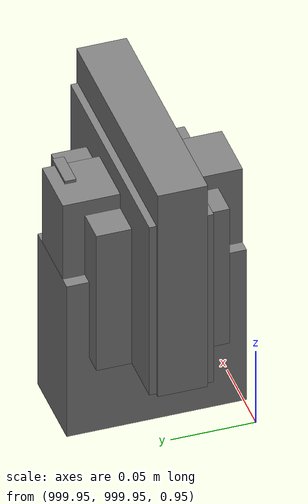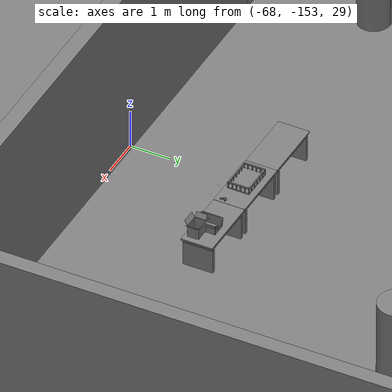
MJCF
<mujoco>
    <option gravity="0.000000000 0.000000000 -9.810000420" timestep="0.0049999999" integrator="implicitfast" density="1.225" viscosity="1.8000001e-05" noslip_iterations="10" iterations="100" sdf_iterations="50">
        <flag multiccd="disable"/>
    </option>
    <size memory="1000M"/>
    <compiler coordinate="local"/>
    <worldbody>
        <light cutoff="30" pos="0 1 1" dir="0 -1 -2"/>
        <light cutoff="30" pos="0 -1 1" dir="0 1 -2"/>
        <body pos="1000.000000000 1000.000000000 1.000000000" euler="0.000000000 0.000000000 180.000000000" name="openloong_gripper_2f85_fix_base_usda_battery_01">
            <geom contype="1" conaffinity="1" density="1000" type="box" material="" rgba="0.500000000 0.500000000 0.500000000 1.000000000" solimp="0.899999976 0.949999988 0.001000000" friction="1.000000000 0.005000000 0.000100000" solref="0.020000000 1.000000000" margin="0" condim="3" group="0" pos="-0.011123657 -0.041940309 0.101691343" quat="1.000000000 0.000000000 0.000000000 0.000000000" size="0.010800000 0.003375000 0.004725000" name="openloong_gripper_2f85_fix_base_usda_geom_DFF05482_CC51_47B6_A13C_A91829FD2527"/>
            <geom contype="1" conaffinity="1" density="1000" type="box" material="" rgba="0.500000000 0.500000000 0.500000000 1.000000000" solimp="0.899999976 0.949999988 0.001000000" friction="1.000000000 0.005000000 0.000100000" solref="0.020000000 1.000000000" margin="0" condim="3" group="0" pos="-0.010876465 -0.044247437 0.047066893" quat="0.998702705 -0.050920475 0.000000000 0.000000000" size="0.009450001 0.002700000 0.024975000" name="openloong_gripper_2f85_fix_base_usda_geom_093D1690_F39C_4450_A92F_6C1FD4FE18DB"/>
            <geom contype="1" conaffinity="1" density="1000" type="box" material="" rgba="0.500000000 0.500000000 0.500000000 1.000000000" solimp="0.899999976 0.949999988 0.001000000" friction="1.000000000 0.005000000 0.000100000" solref="0.020000000 1.000000000" margin="0" condim="3" group="0" pos="-0.001235962 -0.000659180 0.047381196" quat="1.000000000 0.000000000 0.000000000 0.000000000" size="0.039420001 0.039150000 0.047250003" name="openloong_gripper_2f85_fix_base_usda_geom_BAC2692B_EC00_4161_908C_C45E8CE79621"/>
            <geom contype="1" conaffinity="1" density="1000" type="box" material="" rgba="0.500000000 0.500000000 0.500000000 1.000000000" solimp="0.899999976 0.949999988 0.001000000" friction="1.000000000 0.005000000 0.000100000" solref="0.020000000 1.000000000" margin="0" condim="3" group="0" pos="-0.010876465 -0.039138794 0.009851727" quat="1.000000000 0.000000000 0.000000000 0.000000000" size="0.009450001 0.010800000 0.013500000" name="openloong_gripper_2f85_fix_base_usda_geom_CDE78A50_624C_4AB7_9CEF_1FC97CAEDA0E"/>
            <geom contype="1" conaffinity="1" density="1000" type="box" material="" rgba="0.500000000 0.500000000 0.500000000 1.000000000" solimp="0.899999976 0.949999988 0.001000000" friction="1.000000000 0.005000000 0.000100000" solref="0.020000000 1.000000000" margin="0" condim="3" group="0" pos="-0.010876465 -0.041528322 0.071508206" quat="1.000000000 0.000000000 0.000000000 0.000000000" size="0.009450001 0.002700000 0.027000001" name="openloong_gripper_2f85_fix_base_usda_geom_2EA88934_226D_42D3_9AF9_8235C599B8C5"/>
            <freejoint name="openloong_gripper_2f85_fix_base_usda_battery_01_joint"/>
            <site size="0.005000000 0.005000000 0.005000000" rgba="0.500000000 0.500000000 0.500000000 1.000000000" pos="0.000000000 0.000000000 0.000000000" quat="0.999961913 0.008726500 0.000000000 0.000000000" group="0" type="sphere" name="openloong_gripper_2f85_fix_base_usda_battery_01site"/>
        </body>
        <body pos="1000.000000000 1000.000000000 1.000000000" euler="0.000000000 0.000000000 180.000000000" name="openloong_gripper_2f85_fix_base_usda_cpu_fan">
            <geom contype="1" conaffinity="1" density="1000" type="box" material="" rgba="0.500000000 0.500000000 0.500000000 1.000000000" solimp="0.899999976 0.949999988 0.001000000" friction="1.000000000 0.005000000 0.000100000" solref="0.020000000 1.000000000" margin="0" condim="3" group="0" pos="0.000000000 0.000000000 0.070034981" quat="0.000000000 0.000000000 0.000000000 1.000000000" size="0.070700005 0.014699999 0.070700005" name="openloong_gripper_2f85_fix_base_usda_geom_B9527E33_2B02_4954_84E4_3ED205048308"/>
            <freejoint name="openloong_gripper_2f85_fix_base_usda_cpu_fan_joint"/>
            <site size="0.005000000 0.005000000 0.005000000" rgba="0.500000000 0.500000000 0.500000000 1.000000000" pos="0.000000000 0.000000000 0.000000000" quat="0.999961913 0.008726535 0.000000000 0.000000000" group="0" type="sphere" name="openloong_gripper_2f85_fix_base_usda_cpu_fancsite"/>
        </body>
        <body pos="1000.000000000 1000.000000000 1.000000000" euler="0.000000000 0.000000000 180.000000000" name="openloong_gripper_2f85_fix_base_usda_wifi_box">
            <geom contype="1" conaffinity="1" density="1000" type="box" material="" rgba="0.500000000 0.500000000 0.500000000 1.000000000" solimp="0.899999976 0.949999988 0.001000000" friction="1.000000000 0.005000000 0.000100000" solref="0.020000000 1.000000000" margin="0" condim="3" group="0" pos="0.000000000 0.000000000 0.058978677" quat="0.000000000 0.000000047 0.000000000 1.000000000" size="0.068499997 0.018999999 0.059000000" name="openloong_gripper_2f85_fix_base_usda_geom_1D22DB8A_2E9F_4CED_A19F_AC0F78D479AD"/>
            <freejoint name="openloong_gripper_2f85_fix_base_usda_wifi_box_joint"/>
            <site size="0.005000000 0.005000000 0.005000000" rgba="0.500000000 0.500000000 0.500000000 1.000000000" pos="0.000000000 0.000000000 0.000000000" quat="0.999961913 0.008726500 0.000000000 0.000000000" group="0" type="sphere" name="openloong_gripper_2f85_fix_base_usda_wifi_boxsite"/>
        </body>
        <body pos="-66.218376160 -148.902297974 31.167634964" euler="170.558837891 62.333465576 -9.498492241" mocap="true" name="spotlight6_SpotLight"/>
        <body pos="1000.000000000 1000.000000000 1.000000000" euler="0.000011953 0.000005123 -179.999984741" name="openloong_gripper_2f85_fix_base_usda_intel_box">
            <geom contype="1" conaffinity="1" density="1000" type="box" material="" rgba="0.500000000 0.500000000 0.500000000 1.000000000" solimp="0.899999976 0.949999988 0.001000000" friction="1.000000000 0.005000000 0.000100000" solref="0.020000000 1.000000000" margin="0" condim="3" group="0" pos="0.000000000 -0.000067139 0.000082284" quat="0.707106709 0.000000225 0.000000253 0.707106650" size="0.052800003 0.025300000 0.052800003" name="openloong_gripper_2f85_fix_base_usda_geom_189453B5_37D6_49E3_AD42_A2930DABD00F"/>
            <freejoint name="openloong_gripper_2f85_fix_base_usda_intel_box_joint"/>
            <site size="0.005000000 0.005000000 0.005000000" rgba="0.500000000 0.500000000 0.500000000 1.000000000" pos="0.000000000 0.000000000 0.000000000" quat="0.999961913 0.008726500 0.000000000 0.000000000" group="0" type="sphere" name="openloong_gripper_2f85_fix_base_usda_intel_boxsite"/>
        </body>
        <body pos="-66.037940979 -148.989669800 31.171592712" euler="102.063201904 18.256856918 53.218402863" mocap="true" name="spotlight5_SpotLight"/>
        <body pos="1000.000000000 999.999938965 1.000000000" euler="0.000000000 0.000000000 180.000000000" name="openloong_gripper_2f85_fix_base_usda_intelcore_i5">
            <geom contype="1" conaffinity="1" density="1000" type="box" material="" rgba="0.500000000 0.500000000 0.500000000 1.000000000" solimp="0.899999976 0.949999988 0.001000000" friction="1.000000000 0.005000000 0.000100000" solref="0.020000000 1.000000000" margin="0" condim="3" group="0" pos="0.000000000 0.000000000 0.051722717" quat="0.707106709 0.000000000 0.000000000 -0.707106769" size="0.052800000 0.018080002 0.052800000" name="openloong_gripper_2f85_fix_base_usda_geom_4E466AB3_C3FB_43D2_BD2C_B222976F32B6"/>
            <freejoint name="openloong_gripper_2f85_fix_base_usda_intelcore_i5_joint"/>
            <site size="0.005000000 0.005000000 0.005000000" rgba="0.500000000 0.500000000 0.500000000 1.000000000" pos="0.000000000 0.000000000 0.000000000" quat="0.999961913 0.008726534 0.000000000 0.000000000" group="0" type="sphere" name="openloong_gripper_2f85_fix_base_usda_intelcore_i5site"/>
        </body>
        <body pos="-66.223220825 -149.750061035 31.170780182" euler="113.306465149 16.149909973 -168.392868042" mocap="true" name="spotlight1_SpotLight"/>
        <body pos="-64.866622925 -149.383972168 30.183746338" euler="89.999984741 89.999946594 0.000000000" name="openloong_gripper_2f85_fix_base_usda_bluebox_01">
            <geom contype="1" conaffinity="1" density="1000" type="box" material="" rgba="0.500000000 0.500000000 0.500000000 1.000000000" solimp="0.899999976 0.949999988 0.001000000" friction="1.000000000 0.005000000 0.000100000" solref="0.020000000 1.000000000" margin="0" condim="3" group="0" pos="0.276580811 0.187225342 0.000068665" quat="0.707106948 0.000077471 0.707106352 0.000077486" size="0.100000001 0.057999998 0.010000000" name="openloong_gripper_2f85_fix_base_usda_geom_F9F61CC5_AE3D_4D14_9674_34A49DE019C1"/>
            <geom contype="1" conaffinity="1" density="1000" type="box" material="" rgba="0.500000000 0.500000000 0.500000000 1.000000000" solimp="0.899999976 0.949999988 0.001000000" friction="1.000000000 0.005000000 0.000100000" solref="0.020000000 1.000000000" margin="0" condim="3" group="0" pos="0.000000000 0.002883911 0.000000000" quat="0.999999881 0.000000000 0.000000000 0.000000000" size="0.254000008 0.003000000 0.172000006" name="openloong_gripper_2f85_fix_base_usda_geom_1AC3D62F_B5E6_4B12_8DC9_A5D40F37531B"/>
            <geom contype="1" conaffinity="1" density="1000" type="box" material="" rgba="0.500000000 0.500000000 0.500000000 1.000000000" solimp="0.899999976 0.949999988 0.001000000" friction="1.000000000 0.005000000 0.000100000" solref="0.020000000 1.000000000" margin="0" condim="3" group="0" pos="0.000000000 0.124874115 0.173484802" quat="0.999796331 0.020176515 -0.000000015 0.000000030" size="0.259999990 0.119999997 0.007000000" name="openloong_gripper_2f85_fix_base_usda_geom_4DD2A92F_541E_45C5_BEFC_95C37C3AC040"/>
            <geom contype="1" conaffinity="1" density="1000" type="box" material="" rgba="0.500000000 0.500000000 0.500000000 1.000000000" solimp="0.899999976 0.949999988 0.001000000" friction="1.000000000 0.005000000 0.000100000" solref="0.020000000 1.000000000" margin="0" condim="3" group="0" pos="0.000000000 0.124874115 -0.173469543" quat="0.999796331 -0.020176545 -0.000000015 0.000000000" size="0.259999990 0.119999997 0.007000000" name="openloong_gripper_2f85_fix_base_usda_geom_3EB20781_D82C_4F7C_885B_A005C0F5A731"/>
            <geom contype="1" conaffinity="1" density="1000" type="box" material="" rgba="0.500000000 0.500000000 0.500000000 1.000000000" solimp="0.899999976 0.949999988 0.001000000" friction="1.000000000 0.005000000 0.000100000" solref="0.020000000 1.000000000" margin="0" condim="3" group="0" pos="0.000000000 0.214008331 0.188980103" quat="0.999912977 0.013176724 0.000000015 0.000000000" size="0.259999990 0.029999999 0.012500000" name="openloong_gripper_2f85_fix_base_usda_geom_2E95A80E_DFD6_4581_B13C_662E86BBA873"/>
            <geom contype="1" conaffinity="1" density="1000" type="box" material="" rgba="0.500000000 0.500000000 0.500000000 1.000000000" solimp="0.899999976 0.949999988 0.001000000" friction="1.000000000 0.005000000 0.000100000" solref="0.020000000 1.000000000" margin="0" condim="3" group="0" pos="-0.258361816 0.125289917 0.001876831" quat="0.702796936 -0.020792112 0.710783124 0.020769298" size="0.189999998 0.119999997 0.009000000" name="openloong_gripper_2f85_fix_base_usda_geom_7AE8379F_8C97_49C2_B64A_29539F6FEE12"/>
            <geom contype="1" conaffinity="1" density="1000" type="box" material="" rgba="0.500000000 0.500000000 0.500000000 1.000000000" solimp="0.899999976 0.949999988 0.001000000" friction="1.000000000 0.005000000 0.000100000" solref="0.020000000 1.000000000" margin="0" condim="3" group="0" pos="0.000000000 0.214008331 -0.188980103" quat="0.999912977 -0.013176769 0.000000030 0.000000015" size="0.259999990 0.029999999 0.012500000" name="openloong_gripper_2f85_fix_base_usda_geom_82CEB89E_3EAE_40D4_A552_E6D4C8FD8559"/>
            <geom contype="1" conaffinity="1" density="1000" type="box" material="" rgba="0.500000000 0.500000000 0.500000000 1.000000000" solimp="0.899999976 0.949999988 0.001000000" friction="1.000000000 0.005000000 0.000100000" solref="0.020000000 1.000000000" margin="0" condim="3" group="0" pos="-0.276611328 0.187225342 0.000068665" quat="0.707106650 0.000077441 0.707106709 0.000077456" size="0.100000001 0.057999998 0.010000000" name="openloong_gripper_2f85_fix_base_usda_geom_ACCDF89F_5EDF_47F8_9322_34E11E25B6CB"/>
            <geom contype="1" conaffinity="1" density="1000" type="box" material="" rgba="0.500000000 0.500000000 0.500000000 1.000000000" solimp="0.899999976 0.949999988 0.001000000" friction="1.000000000 0.005000000 0.000100000" solref="0.020000000 1.000000000" margin="0" condim="3" group="0" pos="0.258331299 0.125289917 0.001876831" quat="0.702851415 0.018856421 0.710823774 -0.019329369" size="0.189999998 0.119999997 0.009000000" name="openloong_gripper_2f85_fix_base_usda_geom_BEF6D1AE_51D3_4437_9FD7_2D3BA6BBF30B"/>
            <freejoint name="openloong_gripper_2f85_fix_base_usda_bluebox_01_joint"/>
            <site size="0.005000000 0.005000000 0.005000000" rgba="0.500000000 0.500000000 0.500000000 1.000000000" pos="0.000000000 0.000000000 0.000000000" quat="0.999961913 0.008726534 0.000000000 0.000000000" group="0" type="sphere" name="openloong_gripper_2f85_fix_base_usda_bluebox_01site"/>
        </body>
        <body pos="-64.496299744 -149.491867065 30.235729218" euler="0.000000000 0.000000000 89.999946594" name="openloong_gripper_2f85_fix_base_usda_cardboardbox_01">
            <geom contype="1" conaffinity="1" density="1000" type="box" material="" rgba="0.500000000 0.500000000 0.500000000 1.000000000" solimp="0.899999976 0.949999988 0.001000000" friction="1.000000000 0.005000000 0.000100000" solref="0.020000000 1.000000000" margin="0" condim="3" group="0" pos="-0.003166199 -0.004086494 0.005052090" quat="1.000000000 0.000000000 0.000000000 0.000000000" size="0.142499998 0.177500010 0.005000000" name="openloong_gripper_2f85_fix_base_usda_geom_9E2F7D96_4FA8_48A4_8F6C_C980277D3E94"/>
            <geom contype="1" conaffinity="1" density="1000" type="box" material="" rgba="0.500000000 0.500000000 0.500000000 1.000000000" solimp="0.899999976 0.949999988 0.001000000" friction="1.000000000 0.005000000 0.000100000" solref="0.020000000 1.000000000" margin="0" condim="3" group="0" pos="-0.003166199 0.170316696 0.150570869" quat="1.000000000 0.000000000 0.000000000 0.000000000" size="0.142499998 0.005000000 0.149999991" name="openloong_gripper_2f85_fix_base_usda_geom_E2121D10_3A1F_4CE8_B378_2A43E27E63FD"/>
            <geom contype="1" conaffinity="1" density="1000" type="box" material="" rgba="0.500000000 0.500000000 0.500000000 1.000000000" solimp="0.899999976 0.949999988 0.001000000" friction="1.000000000 0.005000000 0.000100000" solref="0.020000000 1.000000000" margin="0" condim="3" group="0" pos="-0.147399902 -0.005307198 0.150570869" quat="1.000000000 0.000000000 0.000000000 0.000000000" size="0.005000000 0.177500010 0.149999991" name="openloong_gripper_2f85_fix_base_usda_geom_C4D9E7EB_ACC1_419B_8B2C_67B9E3E3C548"/>
            <geom contype="1" conaffinity="1" density="1000" type="box" material="" rgba="0.500000000 0.500000000 0.500000000 1.000000000" solimp="0.899999976 0.949999988 0.001000000" friction="1.000000000 0.005000000 0.000100000" solref="0.020000000 1.000000000" margin="0" condim="3" group="0" pos="0.140275955 -0.005307198 0.150570869" quat="1.000000000 0.000000000 0.000000000 0.000000000" size="0.005000000 0.177500010 0.149999991" name="openloong_gripper_2f85_fix_base_usda_geom_36010E37_83F8_42DC_9D6E_F684EB17BE03"/>
            <geom contype="1" conaffinity="1" density="1000" type="box" material="" rgba="0.500000000 0.500000000 0.500000000 1.000000000" solimp="0.899999976 0.949999988 0.001000000" friction="1.000000000 0.005000000 0.000100000" solref="0.020000000 1.000000000" margin="0" condim="3" group="0" pos="-0.003166199 -0.181550980 0.150570869" quat="1.000000000 0.000000000 0.000000000 0.000000000" size="0.142499998 0.005000000 0.149999991" name="openloong_gripper_2f85_fix_base_usda_geom_F3D5D508_5A55_4359_8843_F7F99BE5F2B8"/>
            <freejoint name="openloong_gripper_2f85_fix_base_usda_cardboardbox_01_joint"/>
            <site size="0.005000000 0.005000000 0.005000000" rgba="0.500000000 0.500000000 0.500000000 1.000000000" pos="0.000000000 0.000000000 0.000000000" quat="0.999961913 0.008726535 0.000000000 0.000000000" group="0" type="sphere" name="openloong_gripper_2f85_fix_base_usda_site_E491FC71_7F81_468D_BD92_E5977EB845BC"/>
            <body pos="0.139160156 -0.004048347 0.301930904" euler="-179.999954224 49.383502960 179.999954224" name="openloong_gripper_2f85_fix_base_usda_A1_006">
                <geom contype="1" conaffinity="1" density="1000" type="box" material="" rgba="0.500000000 0.500000000 0.500000000 1.000000000" solimp="0.899999976 0.949999988 0.001000000" friction="1.000000000 0.005000000 0.000100000" solref="0.020000000 1.000000000" margin="0" condim="3" group="0" pos="-0.071587563 0.000009537 0.001745224" quat="0.999999881 0.000000000 0.000000000 0.000000000" size="0.071249999 0.179999992 0.002500000" name="openloong_gripper_2f85_fix_base_usda_geom_03ECE6F7_831F_498F_80E5_CD7A37FB018F"/>
                <joint armature="0" stiffness="0.07" damping="0.0099999998" axis="0.000000 1.000000 0.000000" type="hinge" name="openloong_gripper_2f85_fix_base_usda_A1_006"/>
            </body>
            <body pos="-0.145902634 -0.004086494 0.301938057" euler="-180.000000000 -60.000011444 -180.000000000" name="openloong_gripper_2f85_fix_base_usda_A2_006">
                <geom contype="1" conaffinity="1" density="1000" type="box" material="" rgba="0.500000000 0.500000000 0.500000000 1.000000000" solimp="0.899999976 0.949999988 0.001000000" friction="1.000000000 0.005000000 0.000100000" solref="0.020000000 1.000000000" margin="0" condim="3" group="0" pos="0.071268082 0.000009537 0.002717972" quat="0.000002921 0.000000000 -0.000000030 0.999999881" size="0.071249999 0.179999992 0.002500000" name="openloong_gripper_2f85_fix_base_usda_geom_A0FC33B0_6142_4034_A539_202EF9EF7FB6"/>
                <joint armature="0" stiffness="0.07" damping="0.0099999998" axis="0.000000 1.000000 0.000000" type="hinge" name="openloong_gripper_2f85_fix_base_usda_A2_006"/>
            </body>
            <body pos="-0.003385544 0.175991058 0.301930904" euler="-125.858116150 -0.000004561 0.000002331" name="openloong_gripper_2f85_fix_base_usda_B2_006">
                <geom contype="1" conaffinity="1" density="1000" type="box" material="" rgba="0.500000000 0.500000000 0.500000000 1.000000000" solimp="0.899999976 0.949999988 0.001000000" friction="1.000000000 0.005000000 0.000100000" solref="0.020000000 1.000000000" margin="0" condim="3" group="0" pos="0.000009537 -0.070939064 -0.002470016" quat="0.999614120 0.027776197 -0.000000015 0.000000030" size="0.137500003 0.064999998 0.005000000" name="openloong_gripper_2f85_fix_base_usda_geom_91295055_CAC3_4029_8201_961C10C786B8"/>
                <joint armature="0" stiffness="0.07" damping="0.0099999998" axis="1.000000 0.000000 0.000000" type="hinge" name="openloong_gripper_2f85_fix_base_usda_B2_006"/>
            </body>
            <body pos="-0.003385544 -0.184140205 0.301938057" euler="147.805557251 0.000000000 0.000000000" name="openloong_gripper_2f85_fix_base_usda_B1_006">
                <geom contype="1" conaffinity="1" density="1000" type="box" material="" rgba="0.500000000 0.500000000 0.500000000 1.000000000" solimp="0.899999976 0.949999988 0.001000000" friction="1.000000000 0.005000000 0.000100000" solref="0.020000000 1.000000000" margin="0" condim="3" group="0" pos="-0.000028610 0.070202351 -0.002703667" quat="0.999614179 -0.027776167 0.000000000 0.000000000" size="0.137500003 0.064999998 0.005000000" name="openloong_gripper_2f85_fix_base_usda_geom_D3E22645_B73D_4CBB_87D6_C6805B54CC65"/>
                <joint armature="0" stiffness="0.07" damping="0.0099999998" axis="1.000000 0.000000 0.000000" type="hinge" name="openloong_gripper_2f85_fix_base_usda_B1_006"/>
            </body>
        </body>
        <body pos="-65.882858276 -149.481979370 30.229999542" euler="-64.487716675 0.000000000 0.000000000" name="openloong_gripper_2f85_fix_base_usda_Barcode">
            <geom contype="1" conaffinity="1" density="1000" type="box" material="" rgba="0.500000000 0.500000000 0.500000000 1.000000000" solimp="0.899999976 0.949999988 0.001000000" friction="1.000000000 0.005000000 0.000100000" solref="0.020000000 1.000000000" margin="0" condim="3" group="0" pos="0.000000000 0.013038635 0.001419067" quat="0.000000000 0.000000000 0.000000000 1.000000119" size="0.034000002 0.010000000 0.017999999" name="openloong_gripper_2f85_fix_base_usda_geom_F70BBFBD_C015_469B_A265_6EB895E8002A"/>
            <geom contype="1" conaffinity="1" density="1000" type="box" material="" rgba="0.500000000 0.500000000 0.500000000 1.000000000" solimp="0.899999976 0.949999988 0.001000000" friction="1.000000000 0.005000000 0.000100000" solref="0.020000000 1.000000000" margin="0" condim="3" group="0" pos="0.000000000 -0.035301208 -0.007095337" quat="0.000000000 0.000000000 -0.043619365 0.999048233" size="0.028999999 0.010000000 0.020000000" name="openloong_gripper_2f85_fix_base_usda_geom_571DE627_30D2_43F8_85FB_238A49DF2C84"/>
            <geom contype="1" conaffinity="1" density="1000" type="box" material="" rgba="0.500000000 0.500000000 0.500000000 1.000000000" solimp="0.899999976 0.949999988 0.001000000" friction="1.000000000 0.005000000 0.000100000" solref="0.020000000 1.000000000" margin="0" condim="3" group="0" pos="0.000000000 -0.043411255 -0.011749268" quat="0.922262907 0.386563420 0.000000000 0.000000000" size="0.026000001 0.010000000 0.020000000" name="openloong_gripper_2f85_fix_base_usda_geom_FFA51B99_FCC6_4ECA_AA76_217DA4722942"/>
            <geom contype="1" conaffinity="1" density="1000" type="box" material="" rgba="0.500000000 0.500000000 0.500000000 1.000000000" solimp="0.899999976 0.949999988 0.001000000" friction="1.000000000 0.005000000 0.000100000" solref="0.020000000 1.000000000" margin="0" condim="3" group="0" pos="0.000000000 -0.016967773 -0.031860352" quat="0.000000000 0.000000000 0.000000000 1.000000119" size="0.008000000 0.010000000 0.013000000" name="openloong_gripper_2f85_fix_base_usda_geom_13C23C13_4535_4B3B_9FD3_DB2CA1144762"/>
            <geom contype="1" conaffinity="1" density="1000" type="box" material="" rgba="0.500000000 0.500000000 0.500000000 1.000000000" solimp="0.899999976 0.949999988 0.001000000" friction="1.000000000 0.005000000 0.000100000" solref="0.020000000 1.000000000" margin="0" condim="3" group="0" pos="0.000000000 -0.001869202 0.000312805" quat="0.953716993 0.300705761 0.000000000 0.000000000" size="0.032000002 0.010000000 0.018999999" name="openloong_gripper_2f85_fix_base_usda_geom_2CA2D474_48D0_4A71_90E0_D581EE6CADE3"/>
            <geom contype="1" conaffinity="1" density="1000" type="box" material="" rgba="0.500000000 0.500000000 0.500000000 1.000000000" solimp="0.899999976 0.949999988 0.001000000" friction="1.000000000 0.005000000 0.000100000" solref="0.020000000 1.000000000" margin="0" condim="3" group="0" pos="0.000000000 -0.019531250 -0.003173828" quat="0.953716993 0.300705761 0.000000000 0.000000000" size="0.030999999 0.010000000 0.020000000" name="openloong_gripper_2f85_fix_base_usda_geom_C88424C6_557E_4860_A3D7_C2E912E221CD"/>
            <geom contype="1" conaffinity="1" density="1000" type="box" material="" rgba="0.500000000 0.500000000 0.500000000 1.000000000" solimp="0.899999976 0.949999988 0.001000000" friction="1.000000000 0.005000000 0.000100000" solref="0.020000000 1.000000000" margin="0" condim="3" group="0" pos="0.000000000 -0.035301208 -0.007095337" quat="0.953716993 0.300705761 0.000000000 0.000000000" size="0.028999999 0.010000000 0.020000000" name="openloong_gripper_2f85_fix_base_usda_geom_C4DB11FA_D802_4CDB_A461_F0B5AEBD2242"/>
            <geom contype="1" conaffinity="1" density="1000" type="box" material="" rgba="0.500000000 0.500000000 0.500000000 1.000000000" solimp="0.899999976 0.949999988 0.001000000" friction="1.000000000 0.005000000 0.000100000" solref="0.020000000 1.000000000" margin="0" condim="3" group="0" pos="0.000000000 -0.042617798 -0.071121216" quat="0.000000000 0.000000000 0.000000000 1.000000119" size="0.013000000 0.021000000 0.059999999" name="openloong_gripper_2f85_fix_base_usda_geom_BC45D6B6_B27D_4FCA_BDD9_658D0AE8E632"/>
            <freejoint name="openloong_gripper_2f85_fix_base_usda_Barcode_joint"/>
            <site size="0.005000000 0.005000000 0.005000000" rgba="0.500000000 0.500000000 0.500000000 1.000000000" pos="0.000000000 0.000000000 0.000000000" quat="1.000000000 0.000000000 0.000000000 0.000000000" group="0" type="sphere" name="openloong_gripper_2f85_fix_base_usda_Barcode_site"/>
        </body>
        <body pos="-66.745018005 -149.392349243 30.184000015" euler="0.000000000 0.000000000 89.999946594" name="[22332894392901]_Basket_01">
            <geom contype="1" conaffinity="1" density="1000" type="box" material="" rgba="0.500000000 0.500000000 0.500000000 1.000000000" solimp="0.899999976 0.949999988 0.001000000" friction="1.000000000 0.005000000 0.000100000" solref="0.020000000 1.000000000" margin="0" condim="3" group="0" pos="-0.052425385 0.389207840 0.089787483" quat="0.707107008 0.000000000 0.000000000 0.707106411" size="0.014249999 0.014249999 0.059999999" name="[22332894392901]_geom_F70278BD_29BC_4D38_9738_51AF7D22AE06"/>
            <geom contype="1" conaffinity="1" density="1000" type="box" material="" rgba="0.500000000 0.500000000 0.500000000 1.000000000" solimp="0.899999976 0.949999988 0.001000000" friction="1.000000000 0.005000000 0.000100000" solref="0.020000000 1.000000000" margin="0" condim="3" group="0" pos="0.264015198 -0.133043289 0.089787483" quat="0.707107008 0.000000000 0.000000000 0.707106411" size="0.014249999 0.014249999 0.059999999" name="[22332894392901]_geom_59904601_1D66_40A7_937A_5A5219D79252"/>
            <geom contype="1" conaffinity="1" density="1000" type="box" material="" rgba="0.500000000 0.500000000 0.500000000 1.000000000" solimp="0.899999976 0.949999988 0.001000000" friction="1.000000000 0.005000000 0.000100000" solref="0.020000000 1.000000000" margin="0" condim="3" group="0" pos="-0.264015198 -0.265548706 0.089793205" quat="0.707107008 0.000000000 0.000000000 0.707106411" size="0.014249999 0.014249999 0.059999999" name="[22332894392901]_geom_F6EE851B_0B1D_4751_9ED8_41927F5691FE"/>
            <geom contype="1" conaffinity="1" density="1000" type="box" material="" rgba="0.500000000 0.500000000 0.500000000 1.000000000" solimp="0.899999976 0.949999988 0.001000000" friction="1.000000000 0.005000000 0.000100000" solref="0.020000000 1.000000000" margin="0" condim="3" group="0" pos="-0.160263062 -0.389322281 0.089793205" quat="0.707107008 0.000000000 0.000000000 0.707106411" size="0.014249999 0.014249999 0.059999999" name="[22332894392901]_geom_CE4672FE_F584_4A43_A41A_34832AD84B8D"/>
            <geom contype="1" conaffinity="1" density="1000" type="box" material="" rgba="0.500000000 0.500000000 0.500000000 1.000000000" solimp="0.899999976 0.949999988 0.001000000" friction="1.000000000 0.005000000 0.000100000" solref="0.020000000 1.000000000" margin="0" condim="3" group="0" pos="0.162265778 -0.389322281 0.089787483" quat="0.707107008 0.000000000 0.000000000 0.707106411" size="0.014249999 0.014249999 0.059999999" name="[22332894392901]_geom_F0178272_6EDA_4C41_B428_523DC03C6C34"/>
            <geom contype="1" conaffinity="1" density="1000" type="box" material="" rgba="0.500000000 0.500000000 0.500000000 1.000000000" solimp="0.899999976 0.949999988 0.001000000" friction="1.000000000 0.005000000 0.000100000" solref="0.020000000 1.000000000" margin="0" condim="3" group="0" pos="0.264015198 0.389207840 0.089787483" quat="0.707107008 0.000000000 0.000000000 0.707106411" size="0.014249999 0.014249999 0.059999999" name="[22332894392901]_geom_C8AB67EE_A3C9_4743_85FE_FDBB8F2383A3"/>
            <geom contype="1" conaffinity="1" density="1000" type="box" material="" rgba="0.500000000 0.500000000 0.500000000 1.000000000" solimp="0.899999976 0.949999988 0.001000000" friction="1.000000000 0.005000000 0.000100000" solref="0.020000000 1.000000000" margin="0" condim="3" group="0" pos="-0.264015198 -0.133043289 0.089793205" quat="0.707107008 0.000000000 0.000000000 0.707106411" size="0.014249999 0.014249999 0.059999999" name="[22332894392901]_geom_D30D109C_C1C1_448E_981F_C9668354B633"/>
            <geom contype="1" conaffinity="1" density="1000" type="box" material="" rgba="0.500000000 0.500000000 0.500000000 1.000000000" solimp="0.899999976 0.949999988 0.001000000" friction="1.000000000 0.005000000 0.000100000" solref="0.020000000 1.000000000" margin="0" condim="3" group="0" pos="-0.264026642 0.269256592 0.089793205" quat="0.707107008 0.000000000 0.000000000 0.707106411" size="0.014249999 0.014249999 0.059999999" name="[22332894392901]_geom_BD050A39_ADCA_419B_9C20_22E8EB3779CC"/>
            <geom contype="1" conaffinity="1" density="1000" type="box" material="" rgba="0.500000000 0.500000000 0.500000000 1.000000000" solimp="0.899999976 0.949999988 0.001000000" friction="1.000000000 0.005000000 0.000100000" solref="0.020000000 1.000000000" margin="0" condim="3" group="0" pos="0.054462433 0.389207840 0.089787483" quat="0.707107008 0.000000000 0.000000000 0.707106411" size="0.014249999 0.014249999 0.059999999" name="[22332894392901]_geom_5B78ECC4_E0D6_4409_9F30_9D606FA245EF"/>
            <geom contype="1" conaffinity="1" density="1000" type="box" material="" rgba="0.500000000 0.500000000 0.500000000 1.000000000" solimp="0.899999976 0.949999988 0.001000000" friction="1.000000000 0.005000000 0.000100000" solref="0.020000000 1.000000000" margin="0" condim="3" group="0" pos="0.054462433 -0.389322281 0.089787483" quat="0.707107008 0.000000000 0.000000000 0.707106411" size="0.014249999 0.014249999 0.059999999" name="[22332894392901]_geom_C9548FA6_46A1_4342_A803_C4205B2841F5"/>
            <geom contype="1" conaffinity="1" density="1000" type="box" material="" rgba="0.500000000 0.500000000 0.500000000 1.000000000" solimp="0.899999976 0.949999988 0.001000000" friction="1.000000000 0.005000000 0.000100000" solref="0.020000000 1.000000000" margin="0" condim="3" group="0" pos="0.264015198 0.269256592 0.089793205" quat="0.707107008 0.000000000 0.000000000 0.707106411" size="0.014249999 0.014249999 0.059999999" name="[22332894392901]_geom_14874BF9_2013_427B_8BA5_F7B2254F082C"/>
            <geom contype="1" conaffinity="1" density="1000" type="box" material="" rgba="0.500000000 0.500000000 0.500000000 1.000000000" solimp="0.899999976 0.949999988 0.001000000" friction="1.000000000 0.005000000 0.000100000" solref="0.020000000 1.000000000" margin="0" condim="3" group="0" pos="0.264015198 -0.389322281 0.089787483" quat="0.707107008 0.000000000 0.000000000 0.707106411" size="0.014249999 0.014249999 0.059999999" name="[22332894392901]_geom_1BB9CBCD_69C1_453B_B3DC_C839296F1742"/>
            <geom contype="1" conaffinity="1" density="1000" type="box" material="" rgba="0.500000000 0.500000000 0.500000000 1.000000000" solimp="0.899999976 0.949999988 0.001000000" friction="1.000000000 0.005000000 0.000100000" solref="0.020000000 1.000000000" margin="0" condim="3" group="0" pos="0.000000000 0.000000000 0.015998840" quat="0.707107008 0.000000000 0.000000000 0.707106411" size="0.403499991 0.279000014 0.015750000" name="[22332894392901]_geom_9EA9FC1B_B6BF_478F_AE9D_B97695373BD4"/>
            <geom contype="1" conaffinity="1" density="1000" type="box" material="" rgba="0.500000000 0.500000000 0.500000000 1.000000000" solimp="0.899999976 0.949999988 0.001000000" friction="1.000000000 0.005000000 0.000100000" solref="0.020000000 1.000000000" margin="0" condim="3" group="0" pos="0.000000000 -0.389476776 0.163619041" quat="0.707107008 0.000000000 0.000000000 0.707106411" size="0.015000000 0.277500004 0.015750000" name="[22332894392901]_geom_08F94AA7_17E7_4D33_A817_96855855AED6"/>
            <geom contype="1" conaffinity="1" density="1000" type="box" material="" rgba="0.500000000 0.500000000 0.500000000 1.000000000" solimp="0.899999976 0.949999988 0.001000000" friction="1.000000000 0.005000000 0.000100000" solref="0.020000000 1.000000000" margin="0" condim="3" group="0" pos="0.162265778 0.389207840 0.089787483" quat="0.707107008 0.000000000 0.000000000 0.707106411" size="0.014249999 0.014249999 0.059999999" name="[22332894392901]_geom_4553343F_655B_4AB4_890D_494B2B722E90"/>
            <geom contype="1" conaffinity="1" density="1000" type="box" material="" rgba="0.500000000 0.500000000 0.500000000 1.000000000" solimp="0.899999976 0.949999988 0.001000000" friction="1.000000000 0.005000000 0.000100000" solref="0.020000000 1.000000000" margin="0" condim="3" group="0" pos="0.000000000 0.389471054 0.163619041" quat="0.707107008 0.000000000 0.000000000 0.707106411" size="0.015000000 0.277500004 0.015750000" name="[22332894392901]_geom_F7265128_5FC9_4ADA_BC98_081F33409673"/>
            <geom contype="1" conaffinity="1" density="1000" type="box" material="" rgba="0.500000000 0.500000000 0.500000000 1.000000000" solimp="0.899999976 0.949999988 0.001000000" friction="1.000000000 0.005000000 0.000100000" solref="0.020000000 1.000000000" margin="0" condim="3" group="0" pos="-0.263511658 0.000000000 0.163619041" quat="0.707107008 0.000000000 0.000000000 0.707106411" size="0.403499991 0.015000000 0.015750000" name="[22332894392901]_geom_206D3DC7_6148_4835_B99B_A4E367D33A89"/>
            <geom contype="1" conaffinity="1" density="1000" type="box" material="" rgba="0.500000000 0.500000000 0.500000000 1.000000000" solimp="0.899999976 0.949999988 0.001000000" friction="1.000000000 0.005000000 0.000100000" solref="0.020000000 1.000000000" margin="0" condim="3" group="0" pos="-0.264015198 0.141334534 0.089793205" quat="0.707107008 0.000000000 0.000000000 0.707106411" size="0.014249999 0.014249999 0.059999999" name="[22332894392901]_geom_88FE1658_2D3B_4E81_BB51_53678EB86D37"/>
            <geom contype="1" conaffinity="1" density="1000" type="box" material="" rgba="0.500000000 0.500000000 0.500000000 1.000000000" solimp="0.899999976 0.949999988 0.001000000" friction="1.000000000 0.005000000 0.000100000" solref="0.020000000 1.000000000" margin="0" condim="3" group="0" pos="0.264015198 -0.265548706 0.089787483" quat="0.707107008 0.000000000 0.000000000 0.707106411" size="0.014249999 0.014249999 0.059999999" name="[22332894392901]_geom_003B492F_D17E_4CFA_9566_6A18E32072F8"/>
            <geom contype="1" conaffinity="1" density="1000" type="box" material="" rgba="0.500000000 0.500000000 0.500000000 1.000000000" solimp="0.899999976 0.949999988 0.001000000" friction="1.000000000 0.005000000 0.000100000" solref="0.020000000 1.000000000" margin="0" condim="3" group="0" pos="-0.160263062 0.389207840 0.089787483" quat="0.707107008 0.000000000 0.000000000 0.707106411" size="0.014249999 0.014249999 0.059999999" name="[22332894392901]_geom_0783A136_1B3A_4DEB_9332_056A9C9CAE82"/>
            <geom contype="1" conaffinity="1" density="1000" type="box" material="" rgba="0.500000000 0.500000000 0.500000000 1.000000000" solimp="0.899999976 0.949999988 0.001000000" friction="1.000000000 0.005000000 0.000100000" solref="0.020000000 1.000000000" margin="0" condim="3" group="0" pos="-0.052425385 -0.389322281 0.089787483" quat="0.707107008 0.000000000 0.000000000 0.707106411" size="0.014249999 0.014249999 0.059999999" name="[22332894392901]_geom_162D74F6_2AEB_4DF1_87F8_D6F586D11E72"/>
            <geom contype="1" conaffinity="1" density="1000" type="box" material="" rgba="0.500000000 0.500000000 0.500000000 1.000000000" solimp="0.899999976 0.949999988 0.001000000" friction="1.000000000 0.005000000 0.000100000" solref="0.020000000 1.000000000" margin="0" condim="3" group="0" pos="-0.264026642 -0.389322281 0.089793205" quat="0.707107008 0.000000000 0.000000000 0.707106411" size="0.014249999 0.014249999 0.059999999" name="[22332894392901]_geom_1EA45A0A_C2ED_414E_8F29_24C2419CB22B"/>
            <geom contype="1" conaffinity="1" density="1000" type="box" material="" rgba="0.500000000 0.500000000 0.500000000 1.000000000" solimp="0.899999976 0.949999988 0.001000000" friction="1.000000000 0.005000000 0.000100000" solref="0.020000000 1.000000000" margin="0" condim="3" group="0" pos="0.264015198 0.141334534 0.089787483" quat="0.707107008 0.000000000 0.000000000 0.707106411" size="0.014249999 0.014249999 0.059999999" name="[22332894392901]_geom_8804451A_4C09_4543_9ADD_C9A5F2703F4A"/>
            <geom contype="1" conaffinity="1" density="1000" type="box" material="" rgba="0.500000000 0.500000000 0.500000000 1.000000000" solimp="0.899999976 0.949999988 0.001000000" friction="1.000000000 0.005000000 0.000100000" solref="0.020000000 1.000000000" margin="0" condim="3" group="0" pos="-0.264015198 0.389207840 0.089793205" quat="0.707107008 0.000000000 0.000000000 0.707106411" size="0.014249999 0.014249999 0.059999999" name="[22332894392901]_geom_C955E744_AEC0_4B09_86DA_B0A49995D8B1"/>
            <geom contype="1" conaffinity="1" density="1000" type="box" material="" rgba="0.500000000 0.500000000 0.500000000 1.000000000" solimp="0.899999976 0.949999988 0.001000000" friction="1.000000000 0.005000000 0.000100000" solref="0.020000000 1.000000000" margin="0" condim="3" group="0" pos="0.264015198 0.004480362 0.089787483" quat="0.707107008 0.000000000 0.000000000 0.707106411" size="0.014249999 0.014249999 0.059999999" name="[22332894392901]_geom_46075F9C_131E_4E26_90A5_5B58FB4F5B7D"/>
            <geom contype="1" conaffinity="1" density="1000" type="box" material="" rgba="0.500000000 0.500000000 0.500000000 1.000000000" solimp="0.899999976 0.949999988 0.001000000" friction="1.000000000 0.005000000 0.000100000" solref="0.020000000 1.000000000" margin="0" condim="3" group="0" pos="0.263694763 -0.000011444 0.163619041" quat="0.707107008 0.000000000 0.000000000 0.707106411" size="0.403499991 0.015000000 0.015750000" name="[22332894392901]_geom_E5415442_5568_47EC_A231_B703AB6A868E"/>
            <geom contype="1" conaffinity="1" density="1000" type="box" material="" rgba="0.500000000 0.500000000 0.500000000 1.000000000" solimp="0.899999976 0.949999988 0.001000000" friction="1.000000000 0.005000000 0.000100000" solref="0.020000000 1.000000000" margin="0" condim="3" group="0" pos="-0.264015198 0.004480362 0.089793205" quat="0.707107008 0.000000000 0.000000000 0.707106411" size="0.014249999 0.014249999 0.059999999" name="[22332894392901]_geom_717396E0_942F_4BC4_B14D_406BE7B08771"/>
            <freejoint name="[22332894392901]_joint_EA459BAE_EFB0_45E8_8A91_1C1D035C1903"/>
        </body>
        <body pos="0.000000000 0.000000000 0.000000000" euler="0.000000000 0.000000000 0.000000000" name="Static Objects_Static Objects">
            <geom contype="1" conaffinity="1" density="1000" type="box" material="" rgba="0.500000000 0.500000000 0.500000000 1.000000000" solimp="0.899999976 0.949999988 0.001000000" friction="1.000000000 0.005000000 0.000100000" solref="0.020000000 1.000000000" margin="0" condim="3" group="0" pos="-67.544113159 -149.365814209 29.727830887" quat="0.500000417 0.499999970 0.499999553 0.499999970" size="0.381000012 0.319999993 0.041000001" name="Static Objects_geom_FEC56269_6932_4E2E_96D6_624C16C8680B"/>
            <geom contype="1" conaffinity="1" density="1000" type="box" material="" rgba="0.500000000 0.500000000 0.500000000 1.000000000" solimp="0.899999976 0.949999988 0.001000000" friction="1.000000000 0.005000000 0.000100000" solref="0.020000000 1.000000000" margin="0" condim="3" group="0" pos="-68.239501953 -149.365814209 30.086868286" quat="0.500000417 0.499999970 0.499999553 0.499999970" size="0.370999992 0.039500002 0.745000005" name="Static Objects_geom_B9EED41D_925A_49B3_B92D_6F341706EEB2"/>
            <geom contype="1" conaffinity="1" density="1000" type="box" material="" rgba="0.500000000 0.500000000 0.500000000 1.000000000" solimp="0.899999976 0.949999988 0.001000000" friction="1.000000000 0.005000000 0.000100000" solref="0.020000000 1.000000000" margin="0" condim="3" group="0" pos="-68.239501953 -149.365814209 30.147235870" quat="0.500000417 0.499999970 0.499999553 0.499999970" size="0.400000006 0.022000000 0.800000012" name="Static Objects_geom_2289A84E_3B0C_4EFD_87B1_380D5E03775D"/>
            <geom contype="1" conaffinity="1" density="1000" type="box" material="" rgba="0.500000000 0.500000000 0.500000000 1.000000000" solimp="0.899999976 0.949999988 0.001000000" friction="1.000000000 0.005000000 0.000100000" solref="0.020000000 1.000000000" margin="0" condim="3" group="0" pos="-68.934890747 -149.365814209 29.727830887" quat="0.500000417 0.499999970 0.499999553 0.499999970" size="0.381000012 0.319999993 0.041000001" name="Static Objects_geom_4803006C_1DA5_41FD_9632_794880CAC09D"/>
            <geom contype="1" conaffinity="1" density="1000" type="box" material="" rgba="0.500000000 0.500000000 0.500000000 1.000000000" solimp="0.899999976 0.949999988 0.001000000" friction="1.000000000 0.005000000 0.000100000" solref="0.020000000 1.000000000" margin="0" condim="3" group="0" pos="-68.239501953 -149.365814209 29.561563492" quat="0.500000417 0.499999970 0.499999553 0.499999970" size="0.020000000 0.022000000 0.660000026" name="Static Objects_geom_C725DFAE_69CD_4BDE_B160_9F2F41D7586D"/>
            <geom contype="1" conaffinity="1" density="1000" type="box" material="" rgba="0.500000000 0.500000000 0.500000000 1.000000000" solimp="0.899999976 0.949999988 0.001000000" friction="1.000000000 0.005000000 0.000100000" solref="0.020000000 1.000000000" margin="0" condim="3" group="0" pos="-65.945671082 -149.365814209 29.727830887" quat="0.500000417 0.499999970 0.499999553 0.499999970" size="0.381000012 0.319999993 0.041000001" name="Static Objects_geom_F1121E71_94DF_4881_8A00_D6531B5B7D20"/>
            <geom contype="1" conaffinity="1" density="1000" type="box" material="" rgba="0.500000000 0.500000000 0.500000000 1.000000000" solimp="0.899999976 0.949999988 0.001000000" friction="1.000000000 0.005000000 0.000100000" solref="0.020000000 1.000000000" margin="0" condim="3" group="0" pos="-66.641059875 -149.365814209 30.086868286" quat="0.500000417 0.499999970 0.499999553 0.499999970" size="0.370999992 0.039500002 0.745000005" name="Static Objects_geom_D46C246B_8802_4BEB_A5A2_266F14FE5000"/>
            <geom contype="1" conaffinity="1" density="1000" type="box" material="" rgba="0.500000000 0.500000000 0.500000000 1.000000000" solimp="0.899999976 0.949999988 0.001000000" friction="1.000000000 0.005000000 0.000100000" solref="0.020000000 1.000000000" margin="0" condim="3" group="0" pos="-66.641059875 -149.365814209 30.147235870" quat="0.500000417 0.499999970 0.499999553 0.499999970" size="0.400000006 0.022000000 0.800000012" name="Static Objects_geom_DAC91803_5262_4CB8_9A44_52AE873B42DB"/>
            <geom contype="1" conaffinity="1" density="1000" type="box" material="" rgba="0.500000000 0.500000000 0.500000000 1.000000000" solimp="0.899999976 0.949999988 0.001000000" friction="1.000000000 0.005000000 0.000100000" solref="0.020000000 1.000000000" margin="0" condim="3" group="0" pos="-67.336448669 -149.365814209 29.727830887" quat="0.500000417 0.499999970 0.499999553 0.499999970" size="0.381000012 0.319999993 0.041000001" name="Static Objects_geom_F926290C_061A_4301_97A4_F295BA3830ED"/>
            <geom contype="1" conaffinity="1" density="1000" type="box" material="" rgba="0.500000000 0.500000000 0.500000000 1.000000000" solimp="0.899999976 0.949999988 0.001000000" friction="1.000000000 0.005000000 0.000100000" solref="0.020000000 1.000000000" margin="0" condim="3" group="0" pos="-66.641059875 -149.365814209 29.561563492" quat="0.500000417 0.499999970 0.499999553 0.499999970" size="0.020000000 0.022000000 0.660000026" name="Static Objects_geom_5D66126C_41DD_4996_86CE_FD4538CB80AD"/>
            <geom contype="1" conaffinity="1" density="1000" type="box" material="" rgba="0.500000000 0.500000000 0.500000000 1.000000000" solimp="0.899999976 0.949999988 0.001000000" friction="1.000000000 0.005000000 0.000100000" solref="0.020000000 1.000000000" margin="0" condim="3" group="0" pos="-64.338577271 -149.365814209 29.727830887" quat="0.500000417 0.499999970 0.499999553 0.499999970" size="0.381000012 0.319999993 0.041000001" name="Static Objects_geom_0CE5BBD4_7CF5_4749_A38F_BC67A0042141"/>
            <geom contype="1" conaffinity="1" density="1000" type="box" material="" rgba="0.500000000 0.500000000 0.500000000 1.000000000" solimp="0.899999976 0.949999988 0.001000000" friction="1.000000000 0.005000000 0.000100000" solref="0.020000000 1.000000000" margin="0" condim="3" group="0" pos="-65.033966064 -149.365814209 30.086868286" quat="0.500000417 0.499999970 0.499999553 0.499999970" size="0.370999992 0.039500002 0.745000005" name="Static Objects_geom_95AE3171_5A61_4A76_B22C_B51C3E5DCEB5"/>
            <geom contype="1" conaffinity="1" density="1000" type="box" material="" rgba="0.500000000 0.500000000 0.500000000 1.000000000" solimp="0.899999976 0.949999988 0.001000000" friction="1.000000000 0.005000000 0.000100000" solref="0.020000000 1.000000000" margin="0" condim="3" group="0" pos="-65.033966064 -149.365814209 30.147235870" quat="0.500000417 0.499999970 0.499999553 0.499999970" size="0.400000006 0.022000000 0.800000012" name="Static Objects_geom_41C4B7DB_855B_41CD_9287_489FC548C22D"/>
            <geom contype="1" conaffinity="1" density="1000" type="box" material="" rgba="0.500000000 0.500000000 0.500000000 1.000000000" solimp="0.899999976 0.949999988 0.001000000" friction="1.000000000 0.005000000 0.000100000" solref="0.020000000 1.000000000" margin="0" condim="3" group="0" pos="-65.729354858 -149.365814209 29.727830887" quat="0.500000417 0.499999970 0.499999553 0.499999970" size="0.381000012 0.319999993 0.041000001" name="Static Objects_geom_4B0F4B01_1075_4DE1_85EE_41E3FDDED367"/>
            <geom contype="1" conaffinity="1" density="1000" type="box" material="" rgba="0.500000000 0.500000000 0.500000000 1.000000000" solimp="0.899999976 0.949999988 0.001000000" friction="1.000000000 0.005000000 0.000100000" solref="0.020000000 1.000000000" margin="0" condim="3" group="0" pos="-65.033966064 -149.365814209 29.561563492" quat="0.500000417 0.499999970 0.499999553 0.499999970" size="0.020000000 0.022000000 0.660000026" name="Static Objects_geom_D6403AF8_34F9_4CFC_8558_FFF9294E8F7F"/>
            <geom contype="1" conaffinity="1" density="1000" type="box" material="" rgba="0.500000000 0.500000000 0.500000000 1.000000000" solimp="0.899999976 0.949999988 0.001000000" friction="1.000000000 0.005000000 0.000100000" solref="0.020000000 1.000000000" margin="0" condim="3" group="0" pos="-61.754566193 -137.853729248 33.906845093" quat="0.707107067 0.000000000 0.000000000 0.707106471" size="0.759999990 0.759999990 4.500000000" name="Static Objects_geom_53BD4BDB_DDB4_4E17_8865_7290E891D1B3"/>
            <geom contype="1" conaffinity="1" density="1000" type="box" material="" rgba="0.500000000 0.500000000 0.500000000 1.000000000" solimp="0.899999976 0.949999988 0.001000000" friction="1.000000000 0.005000000 0.000100000" solref="0.020000000 1.000000000" margin="0" condim="3" group="0" pos="-57.511135101 -144.927108765 31.707921982" quat="1.000000000 0.000000000 0.000000000 0.000000000" size="0.200000003 8.000000000 2.299999952" name="Static Objects_geom_87B08D03_5F6C_4ADD_98DA_B349968236AF"/>
            <geom contype="1" conaffinity="1" density="1000" type="box" material="" rgba="0.500000000 0.500000000 0.500000000 1.000000000" solimp="0.899999976 0.949999988 0.001000000" friction="1.000000000 0.005000000 0.000100000" solref="0.020000000 1.000000000" margin="0" condim="3" group="0" pos="-80.517646790 -157.574050903 31.688196182" quat="0.707107067 0.000000000 0.000000000 0.707106471" size="0.600000024 0.600000024 2.299999952" name="Static Objects_geom_DC65BCBE_C61C_416E_B73D_0C247D2BCE07"/>
            <geom contype="1" conaffinity="1" density="1000" type="box" material="" rgba="0.500000000 0.500000000 0.500000000 1.000000000" solimp="0.899999976 0.949999988 0.001000000" friction="1.000000000 0.005000000 0.000100000" solref="0.020000000 1.000000000" margin="0" condim="3" group="0" pos="-80.711044312 -147.414932251 31.666158676" quat="1.000000000 0.000000000 0.000000000 0.000000000" size="0.200000003 10.000000000 2.299999952" name="Static Objects_geom_C1B87EF8_4FE7_4A17_AF20_8F587BB9F88C"/>
            <geom contype="1" conaffinity="1" density="1000" type="box" material="" rgba="0.500000000 0.500000000 0.500000000 1.000000000" solimp="0.899999976 0.949999988 0.001000000" friction="1.000000000 0.005000000 0.000100000" solref="0.020000000 1.000000000" margin="0" condim="3" group="0" pos="-57.687217712 -137.434692383 31.688196182" quat="0.707107067 0.000000000 0.000000000 0.707106471" size="0.600000024 0.600000024 2.299999952" name="Static Objects_geom_B2A27E6E_8AE3_4E55_ABF3_72BA4D88B47B"/>
            <geom contype="1" conaffinity="1" density="1000" type="box" material="" rgba="0.500000000 0.500000000 0.500000000 1.000000000" solimp="0.899999976 0.949999988 0.001000000" friction="1.000000000 0.005000000 0.000100000" solref="0.020000000 1.000000000" margin="0" condim="3" group="0" pos="-69.537033081 -140.263229370 31.714921951" quat="0.707107067 0.000000000 0.000000000 0.707106471" size="0.759999990 4.500000000 2.299999952" name="Static Objects_geom_102E89D5_D0FF_4F30_8756_3AA85D9228E6"/>
            <geom contype="1" conaffinity="1" density="1000" type="box" material="" rgba="0.500000000 0.500000000 0.500000000 1.000000000" solimp="0.899999976 0.949999988 0.001000000" friction="1.000000000 0.005000000 0.000100000" solref="0.020000000 1.000000000" margin="0" condim="3" group="0" pos="-80.073638916 -137.853713989 33.906845093" quat="0.707107067 0.000000000 0.000000000 0.707106471" size="0.759999990 0.759999990 4.500000000" name="Static Objects_geom_98C07741_B7C8_4C22_848C_8062673A0D62"/>
            <geom contype="1" conaffinity="1" density="1000" type="box" material="" rgba="0.500000000 0.500000000 0.500000000 1.000000000" solimp="0.899999976 0.949999988 0.001000000" friction="1.000000000 0.005000000 0.000100000" solref="0.020000000 1.000000000" margin="0" condim="3" group="0" pos="-73.406707764 -155.734664917 31.707921982" quat="1.000000000 0.000000000 0.000000000 0.000000000" size="0.200000003 3.000000000 2.299999952" name="Static Objects_geom_A613B888_3558_4BF0_8185_B980F47B842D"/>
            <geom contype="1" conaffinity="1" density="1000" type="box" material="" rgba="0.500000000 0.500000000 0.500000000 1.000000000" solimp="0.899999976 0.949999988 0.001000000" friction="1.000000000 0.005000000 0.000100000" solref="0.020000000 1.000000000" margin="0" condim="3" group="0" pos="-68.497543335 -137.448257446 31.707921982" quat="0.707107067 0.000000000 0.000000000 0.707106471" size="0.200000003 14.000000000 2.299999952" name="Static Objects_geom_60CECADD_0B2E_4BC0_8D7F_5A8BC73A9E03"/>
            <geom contype="1" conaffinity="1" density="1000" type="cylinder" material="" rgba="0.500000000 0.500000000 0.500000000 1.000000000" solimp="0.899999976 0.949999988 0.001000000" friction="1.000000000 0.005000000 0.000100000" solref="0.020000000 1.000000000" margin="0" condim="3" group="0" pos="-68.868522644 -142.134506226 31.711090088" quat="0.707107067 0.000000000 0.000000000 0.707106471" size="0.509999990 2.299999952 1.000000000" name="Static Objects_geom_282A8585_20A2_40D5_87B9_6E0FC9921E06"/>
            <geom contype="1" conaffinity="1" density="1000" type="plane" material="" rgba="0.500000000 0.500000000 0.500000000 1.000000000" solimp="0.899999976 0.949999988 0.001000000" friction="1.000000000 0.005000000 0.000100000" solref="0.020000000 1.000000000" margin="0" condim="3" group="0" pos="-72.873703003 -147.131927490 29.409669876" quat="1.000000000 0.000000000 0.000000000 0.000000000" size="18.000000000 14.000000000 1.000000000" name="Static Objects_geom_AFE63D3E_99BD_4C61_B1DB_656DCF70722C"/>
            <geom contype="1" conaffinity="1" density="1000" type="box" material="" rgba="0.500000000 0.500000000 0.500000000 1.000000000" solimp="0.899999976 0.949999988 0.001000000" friction="1.000000000 0.005000000 0.000100000" solref="0.020000000 1.000000000" margin="0" condim="3" group="0" pos="-79.943580627 -157.782272339 31.707921982" quat="0.707107067 0.000000000 0.000000000 0.707106471" size="0.200000003 7.000000000 2.299999952" name="Static Objects_geom_93BE6864_B622_403F_9362_120153E09243"/>
            <geom contype="1" conaffinity="1" density="1000" type="box" material="" rgba="0.500000000 0.500000000 0.500000000 1.000000000" solimp="0.899999976 0.949999988 0.001000000" friction="1.000000000 0.005000000 0.000100000" solref="0.020000000 1.000000000" margin="0" condim="3" group="0" pos="-65.421028137 -152.903442383 31.707921982" quat="0.707107067 0.000000000 0.000000000 0.707106471" size="0.200000003 7.800000191 2.299999952" name="Static Objects_geom_9517D7C1_6B88_461C_8254_3194248150CA"/>
            <geom contype="1" conaffinity="1" density="1000" type="box" material="" rgba="0.500000000 0.500000000 0.500000000 1.000000000" solimp="0.899999976 0.949999988 0.001000000" friction="1.000000000 0.005000000 0.000100000" solref="0.020000000 1.000000000" margin="0" condim="3" group="0" pos="-74.776908875 -149.964416504 31.688196182" quat="1.000000000 0.000000000 0.000000000 0.000000000" size="0.600000024 0.409999996 2.299999952" name="Static Objects_geom_6476716E_1CDC_4557_9854_69968FA42C91"/>
            <geom contype="1" conaffinity="1" density="1000" type="cylinder" material="" rgba="0.500000000 0.500000000 0.500000000 1.000000000" solimp="0.899999976 0.949999988 0.001000000" friction="1.000000000 0.005000000 0.000100000" solref="0.020000000 1.000000000" margin="0" condim="3" group="0" pos="-60.161884308 -142.134506226 31.711090088" quat="0.707107067 0.000000000 0.000000000 0.707106471" size="0.509999990 2.299999952 1.000000000" name="Static Objects_geom_4E838331_F497_4C53_B6DD_7C33742BB50F"/>
            <geom contype="1" conaffinity="1" density="1000" type="cylinder" material="" rgba="0.500000000 0.500000000 0.500000000 1.000000000" solimp="0.899999976 0.949999988 0.001000000" friction="1.000000000 0.005000000 0.000100000" solref="0.020000000 1.000000000" margin="0" condim="3" group="0" pos="-75.382453918 -149.963455200 31.711090088" quat="0.707107067 0.000000000 0.000000000 0.707106471" size="0.409999996 2.299999952 1.000000000" name="Static Objects_geom_22074F3A_671E_4934_891B_A15C48033FB2"/>
            <geom contype="1" conaffinity="1" density="1000" type="cylinder" material="" rgba="0.500000000 0.500000000 0.500000000 1.000000000" solimp="0.899999976 0.949999988 0.001000000" friction="1.000000000 0.005000000 0.000100000" solref="0.020000000 1.000000000" margin="0" condim="3" group="0" pos="-74.154960632 -149.963455200 31.711090088" quat="0.707107067 0.000000000 0.000000000 0.707106471" size="0.409999996 2.299999952 1.000000000" name="Static Objects_geom_3B55E5F5_314B_4861_A1C0_B190576F8F7A"/>
            <geom contype="1" conaffinity="1" density="1000" type="cylinder" material="" rgba="0.500000000 0.500000000 0.500000000 1.000000000" solimp="0.899999976 0.949999988 0.001000000" friction="1.000000000 0.005000000 0.000100000" solref="0.020000000 1.000000000" margin="0" condim="3" group="0" pos="-77.566612244 -142.134506226 31.711090088" quat="0.707107067 0.000000000 0.000000000 0.707106471" size="0.509999990 2.299999952 1.000000000" name="Static Objects_geom_65299321_73D3_4A90_9ED2_77503DF39C25"/>
        </body>
        <body pos="-66.291030884 -149.869689941 29.018842697" euler="0.000000000 0.000000000 89.999946594" mocap="true" name="openloong_gripper_2f85_fix_base_usda_leftHandMocap"/>
        <body pos="-66.291030884 -149.869689941 29.018842697" euler="0.000000000 0.000000000 89.999946594" mocap="true" name="openloong_gripper_2f85_fix_base_usda_rightHandMocap"/>
        <body pos="-66.291030884 -149.869689941 30.218843460" euler="0.000000000 0.000000000 89.999946594" name="openloong_gripper_2f85_fix_base_usda_base_link">
            <geom contype="1" conaffinity="1" density="1000" type="mesh" material="" rgba="0.783999979 0.783999979 0.783999979 1.000000000" solimp="0.899999976 0.949999988 0.001000000" friction="1.000000000 0.005000000 0.000100000" solref="0.020000000 1.000000000" margin="0" condim="3" group="3" mesh="base_link" pos="0.000000000 0.000000000 0.000000000" quat="1.000000000 0.000000000 0.000000000 0.000000000" size="1.000000000 1.000000000 1.000000000" name="openloong_gripper_2f85_fix_base_usda__geom_7_906DE96B_8E63_4D48_B7EC_8D3715540E8A"/>
            <site size="0.005000000 0.005000000 0.005000000" rgba="0.500000000 0.500000000 0.500000000 1.000000000" pos="0.000000000 0.000000000 0.000000000" quat="1.000000000 0.000000000 0.000000000 0.000000000" group="0" type="sphere" name="openloong_gripper_2f85_fix_base_usda_imu"/>
            <inertial mass="22.447001" pos="-0.005664100 -0.001336700 0.238289997" diaginertia="0.374352545 0.277180195 0.220617250" quat="0.999247074 0.035235517 -0.015086859 0.006023135"/>
            <body pos="0.000000000 0.000000000 0.299997330" euler="0.000000000 0.000000000 0.000000000" name="openloong_gripper_2f85_fix_base_usda_dummy_body">
                <geom contype="1" conaffinity="1" density="1000" type="sphere" material="" rgba="0.783999979 0.783999979 0.783999979 1.000000000" solimp="0.899999976 0.949999988 0.001000000" friction="1.000000000 0.005000000 0.000100000" solref="0.020000000 1.000000000" margin="0" condim="3" group="3" pos="0.000000000 0.000000000 0.000000000" quat="1.000000000 0.000000000 0.000000000 0.000000000" size="0.010000000 0.000000000 0.000000000" name="openloong_gripper_2f85_fix_base_usda__geom_8_570EBDD2_4782_45C6_8672_C642BD7A8EC3"/>
                <joint armature="0.0099999998" stiffness="0" damping="0.1" axis="0.000000 0.000000 1.000000" type="hinge" name="openloong_gripper_2f85_fix_base_usda_dummy_joint"/>
                <site size="0.010000000 0.005000000 0.005000000" rgba="0.500000000 0.500000000 0.500000000 1.000000000" pos="0.000000000 0.000000000 0.000000000" quat="1.000000000 0.000000000 0.000000000 0.000000000" group="3" type="sphere" name="openloong_gripper_2f85_fix_base_usda_dummy_site"/>
            </body>
            <body pos="0.009002686 0.000000000 0.406400681" euler="0.000000000 0.000000000 0.000000000" name="openloong_gripper_2f85_fix_base_usda_Link_head_yaw">
                <geom contype="1" conaffinity="1" density="1000" type="mesh" material="" rgba="0.783999979 0.783999979 0.783999979 1.000000000" solimp="0.899999976 0.949999988 0.001000000" friction="1.000000000 0.005000000 0.000100000" solref="0.020000000 1.000000000" margin="0" condim="3" group="3" mesh="Link_head_yaw" pos="0.000000000 0.000000000 0.000000000" quat="1.000000000 0.000000000 0.000000000 0.000000000" size="1.000000000 1.000000000 1.000000000" name="openloong_gripper_2f85_fix_base_usda__geom_10_09496DDD_75AC_42A0_950F_1474BEBACC04"/>
                <inertial mass="0.84249002" pos="0.000000000 -0.002081400 0.044801001" diaginertia="0.000700588 0.000629000 0.000553812" quat="0.706933022 -0.015675601 0.015677100 0.706933022"/>
                <body pos="0.000000000 -0.034599304 0.048500061" euler="0.000000000 0.000000000 0.000000000" name="openloong_gripper_2f85_fix_base_usda_Link_head_pitch">
                    <geom contype="1" conaffinity="1" density="1000" type="mesh" material="" rgba="0.783999979 0.783999979 0.783999979 1.000000000" solimp="0.899999976 0.949999988 0.001000000" friction="1.000000000 0.005000000 0.000100000" solref="0.020000000 1.000000000" margin="0" condim="3" group="3" mesh="Link_head_pitch" pos="0.000000000 0.000000000 0.000000000" quat="1.000000000 0.000000000 0.000000000 0.000000000" size="1.000000000 1.000000000 1.000000000" name="openloong_gripper_2f85_fix_base_usda__geom_12_E0128EC9_F776_483E_8BDA_6A6AA39B692C"/>
                    <inertial mass="1.3943" pos="0.020569000 0.033004001 0.125000000" diaginertia="0.006381400 0.006289940 0.004481460" quat="0.973390222 0.008406822 0.228157058 0.019624906"/>
                    <body pos="0.000000000 0.029998779 0.000000000" euler="0.000000000 0.000000000 0.000000000" name="openloong_gripper_2f85_fix_base_usda_neck_center_body">
                        <site size="0.010000000 0.005000000 0.005000000" rgba="0.500000000 0.500000000 0.500000000 1.000000000" pos="0.000000000 0.000000000 0.000000000" quat="1.000000000 0.000000000 0.000000000 0.000000000" group="3" type="sphere" name="openloong_gripper_2f85_fix_base_usda_neck_center_site"/>
                        <body pos="0.020004272 0.000000000 0.149999619" euler="-0.000002229 39.998176575 -90.000205994" name="openloong_gripper_2f85_fix_base_usda_camera_head">
                            <site size="0.010000000 0.005000000 0.005000000" rgba="0.500000000 0.500000000 0.500000000 1.000000000" pos="0.000000000 0.000000000 0.000000000" quat="1.000000000 0.000000000 0.000000000 0.000000000" group="3" type="sphere" name="openloong_gripper_2f85_fix_base_usda_camera_head_site"/>
                        </body>
                    </body>
                </body>
            </body>
            <body pos="0.003997803 -0.161598206 0.392200470" euler="0.000000000 0.000000000 0.000000000" name="openloong_gripper_2f85_fix_base_usda_Link_arm_r_01">
                <geom contype="1" conaffinity="1" density="1000" type="mesh" material="" rgba="0.783999979 0.783999979 0.783999979 1.000000000" solimp="0.899999976 0.949999988 0.001000000" friction="1.000000000 0.005000000 0.000100000" solref="0.020000000 1.000000000" margin="0" condim="3" group="3" mesh="Link_arm_r_01" pos="0.000000000 0.000000000 0.000000000" quat="1.000000000 0.000000000 0.000000000 0.000000000" size="1.000000000 1.000000000 1.000000000" name="openloong_gripper_2f85_fix_base_usda__geom_14_642CBA62_4711_4A39_BEDE_1DD5A36BB7BC"/>
                <joint armature="0.0099999998" stiffness="0" damping="1" axis="0.000000 -1.000000 0.000000" limited="true" range="-170.000015259 170.000015259" type="hinge" name="openloong_gripper_2f85_fix_base_usda_J_arm_r_01"/>
                <inertial mass="0.75641" pos="0.004494600 -0.038293999 -0.000001874" diaginertia="0.000842990 0.000803050 0.000587120" quat="-0.000163502 0.707098067 0.000812463 0.707115054"/>
                <body pos="-0.041992188 -0.041000366 0.000000000" euler="0.000000000 0.000000000 0.000000000" name="openloong_gripper_2f85_fix_base_usda_Link_arm_r_02">
                    <geom contype="1" conaffinity="1" density="1000" type="mesh" material="" rgba="0.783999979 0.783999979 0.783999979 1.000000000" solimp="0.899999976 0.949999988 0.001000000" friction="1.000000000 0.005000000 0.000100000" solref="0.020000000 1.000000000" margin="0" condim="3" group="3" mesh="Link_arm_r_02" pos="0.000000000 0.000000000 0.000000000" quat="1.000000000 0.000000000 0.000000000 0.000000000" size="1.000000000 1.000000000 1.000000000" name="openloong_gripper_2f85_fix_base_usda__geom_16_C7B44F6D_7FBC_403B_9CB4_EF9EC765971D"/>
                    <joint armature="0.0099999998" stiffness="0" damping="1" axis="-1.000000 0.000000 0.000000" limited="true" range="-105.000244141 105.000244141" type="hinge" name="openloong_gripper_2f85_fix_base_usda_J_arm_r_02"/>
                    <inertial mass="0.98500001" pos="0.041999999 -0.067430697 0.000000000" diaginertia="0.002262690 0.001730990 0.001154020" quat="0.500000000 0.500000000 -0.500000000 0.500000000"/>
                    <body pos="0.041992188 -0.122596741 0.000000000" euler="0.000000000 0.000000000 0.000000000" name="openloong_gripper_2f85_fix_base_usda_Link_arm_r_03">
                        <geom contype="1" conaffinity="1" density="1000" type="mesh" material="" rgba="0.783999979 0.783999979 0.783999979 1.000000000" solimp="0.899999976 0.949999988 0.001000000" friction="1.000000000 0.005000000 0.000100000" solref="0.020000000 1.000000000" margin="0" condim="3" group="3" mesh="Link_arm_r_03" pos="0.000000000 0.000000000 0.000000000" quat="1.000000000 0.000000000 0.000000000 0.000000000" size="1.000000000 1.000000000 1.000000000" name="openloong_gripper_2f85_fix_base_usda__geom_18_4CA1A108_CB25_47EC_8F2E_BE2020FC0F0A"/>
                        <joint armature="0.0099999998" stiffness="0" damping="1" axis="0.000000 -1.000000 0.000000" limited="true" range="-170.000015259 170.000015259" type="hinge" name="openloong_gripper_2f85_fix_base_usda_J_arm_r_03"/>
                        <inertial mass="0.95899999" pos="-0.001413580 -0.164663002 0.020757901" diaginertia="0.002101340 0.002064590 0.000754802" quat="0.560480952 0.454391927 -0.443732947 0.531497955"/>
                        <body pos="0.035293579 -0.177406311 0.023998260" euler="0.000000000 0.000000000 0.000000000" name="openloong_gripper_2f85_fix_base_usda_Link_arm_r_04">
                            <geom contype="1" conaffinity="1" density="1000" type="mesh" material="" rgba="0.783999979 0.783999979 0.783999979 1.000000000" solimp="0.899999976 0.949999988 0.001000000" friction="1.000000000 0.005000000 0.000100000" solref="0.020000000 1.000000000" margin="0" condim="3" group="3" mesh="Link_arm_r_04" pos="0.000000000 0.000000000 0.000000000" quat="1.000000000 0.000000000 0.000000000 0.000000000" size="1.000000000 1.000000000 1.000000000" name="openloong_gripper_2f85_fix_base_usda__geom_20_C9B03E7D_0598_4F60_B665_6E8B1C918CE0"/>
                            <joint armature="0.0099999998" stiffness="0" damping="1" axis="-1.000000 0.000000 0.000000" limited="true" range="0.000000000 170.000015259" type="hinge" name="openloong_gripper_2f85_fix_base_usda_J_arm_r_04"/>
                            <inertial mass="0.60000002" pos="-0.038727000 -0.060766999 -0.021003000" diaginertia="0.001092610 0.000712422 0.000645102" quat="0.327701002 0.632602990 -0.467366993 0.523443997"/>
                            <body pos="-0.035293579 -0.103492737 -0.023998260" euler="0.000000000 0.000000000 0.000000000" name="openloong_gripper_2f85_fix_base_usda_Link_arm_r_05">
                                <geom contype="1" conaffinity="1" density="1000" type="mesh" material="" rgba="0.783999979 0.783999979 0.783999979 1.000000000" solimp="0.899999976 0.949999988 0.001000000" friction="1.000000000 0.005000000 0.000100000" solref="0.020000000 1.000000000" margin="0" condim="3" group="3" mesh="Link_arm_r_05" pos="0.000000000 0.000000000 0.000000000" quat="1.000000000 0.000000000 0.000000000 0.000000000" size="1.000000000 1.000000000 1.000000000" name="openloong_gripper_2f85_fix_base_usda__geom_22_AAFB92D5_9B82_46CE_B6CA_87EDCDA4439A"/>
                                <joint armature="0.0099999998" stiffness="0" damping="1" axis="0.000000 -1.000000 0.000000" limited="true" range="-170.000015259 170.000015259" type="hinge" name="openloong_gripper_2f85_fix_base_usda_J_arm_r_05"/>
                                <inertial mass="0.68976003" pos="0.000032712 -0.068658002 -0.000111780" diaginertia="0.002522510 0.002411100 0.000448695" quat="0.707660973 0.706543028 -0.002603360 0.002470550"/>
                                <body pos="-0.026489258 -0.196502686 0.000000000" euler="0.000000000 0.000000000 0.000000000" name="openloong_gripper_2f85_fix_base_usda_Link_arm_r_06">
                                    <geom contype="1" conaffinity="1" density="1000" type="mesh" material="" rgba="0.783999979 0.783999979 0.783999979 1.000000000" solimp="0.899999976 0.949999988 0.001000000" friction="1.000000000 0.005000000 0.000100000" solref="0.020000000 1.000000000" margin="0" condim="3" group="3" mesh="Link_arm_r_06" pos="0.000000000 0.000000000 0.000000000" quat="1.000000000 0.000000000 0.000000000 0.000000000" size="1.000000000 1.000000000 1.000000000" name="openloong_gripper_2f85_fix_base_usda__geom_24_7B6E38BB_F1EE_41BA_865E_32C31F750B0A"/>
                                    <joint armature="0.0099999998" stiffness="0" damping="1" axis="1.000000 0.000000 0.000000" limited="true" range="-105.000244141 105.000244141" type="hinge" name="openloong_gripper_2f85_fix_base_usda_J_arm_r_06"/>
                                    <inertial mass="0.28" pos="0.026078001 -0.000000896 0.001663700" diaginertia="0.000156930 0.000145601 0.000104979" quat="0.707080841 0.001851080 0.001883810 0.707127810"/>
                                    <body pos="0.026489258 0.000000000 0.031799316" euler="0.000000000 0.000000000 0.000000000" name="openloong_gripper_2f85_fix_base_usda_Link_arm_r_07">
                                        <geom contype="1" conaffinity="1" density="1000" type="mesh" material="" rgba="0.783999979 0.783999979 0.783999979 1.000000000" solimp="0.899999976 0.949999988 0.001000000" friction="1.000000000 0.005000000 0.000100000" solref="0.020000000 1.000000000" margin="0" condim="3" group="3" mesh="Link_arm_r_07" pos="0.000000000 0.000000000 0.000000000" quat="1.000000000 0.000000000 0.000000000 0.000000000" size="1.000000000 1.000000000 1.000000000" name="openloong_gripper_2f85_fix_base_usda__geom_26_6C021852_1B32_4AC5_8A71_DDF21375A9C9"/>
                                        <joint armature="0.0099999998" stiffness="0" damping="1" axis="0.000000 0.000000 1.000000" limited="true" range="-60.000133514 60.000133514" type="hinge" name="openloong_gripper_2f85_fix_base_usda_J_arm_r_07"/>
                                        <inertial mass="0.61353999" pos="-0.007859000 -0.158170000 -0.027736001" diaginertia="0.003037610 0.002570910 0.000729379" quat="0.427542925 0.443532884 -0.553093910 0.560867906"/>
                                        <body pos="0.000000000 0.286994934 -0.270000458" euler="150.000350952 -0.000001649 -0.000000442" name="openloong_gripper_2f85_fix_base_usda_camera_wrist_r">
                                            <site size="0.010000000 0.005000000 0.005000000" rgba="0.500000000 0.500000000 0.500000000 1.000000000" pos="0.000000000 0.000000000 0.000000000" quat="1.000000000 0.000000000 0.000000000 0.000000000" group="3" type="sphere" name="openloong_gripper_2f85_fix_base_usda_camera_wrist_r_site"/>
                                        </body>
                                        <body pos="0.000000000 -0.220008850 -0.033002853" euler="0.000000000 0.000000000 179.999969482" name="openloong_gripper_2f85_fix_base_usda_ee_center_body_r">
                                            <site size="0.010000000 0.005000000 0.005000000" rgba="0.500000000 0.500000000 0.500000000 1.000000000" pos="0.000000000 0.000000000 0.000000000" quat="1.000000000 0.000000000 0.000000000 0.000000000" group="3" type="sphere" name="openloong_gripper_2f85_fix_base_usda_ee_center_site_r"/>
                                        </body>
                                        <body pos="0.000000000 -0.066001892 -0.031000137" euler="89.999984741 0.000000000 180.000000000" name="openloong_gripper_2f85_fix_base_usda_zbr_base_link">
                                            <geom contype="1" conaffinity="1" density="1000" type="mesh" material="" rgba="0.783999979 0.783999979 0.783999979 1.000000000" solimp="0.899999976 0.949999988 0.001000000" friction="1.000000000 0.005000000 0.000100000" solref="0.020000000 1.000000000" margin="0" condim="3" group="3" mesh="base" pos="0.000000000 0.000003815 -0.000007629" quat="1.000000000 0.000000000 0.000000000 0.000000000" size="1.000000238 1.000000238 1.000000238" name="openloong_gripper_2f85_fix_base_usda__geom_30_B5B0D1A1_FDA6_4E19_B591_AA11972C7E2D"/>
                                            <inertial mass="0.77744102" pos="0.000000000 -0.000027039 0.035467502" diaginertia="0.000260285 0.000225381 0.000152708" quat="0.999998808 -0.001528488 0.000000000 0.000000000"/>
                                            <body pos="-0.030609138 0.004745484 0.065696731" euler="-89.999984741 -0.000000000 0.000000000" name="openloong_gripper_2f85_fix_base_usda_r_left_driver">
                                                <geom contype="1" conaffinity="1" density="1000" type="mesh" material="" rgba="0.783999979 0.783999979 0.783999979 1.000000000" solimp="0.899999976 0.949999988 0.001000000" friction="1.000000000 0.005000000 0.000100000" solref="0.020000000 1.000000000" margin="0" condim="3" group="3" mesh="driver" pos="0.030609138 0.054901138 -0.004699708" quat="0.707106829 0.707106709 0.000000000 -0.000000000" size="1.000000238 1.000000238 1.000000238" name="openloong_gripper_2f85_fix_base_usda__geom_32_D8CB09F4_B9A0_4D9E_9C01_480CDA8F8A9F"/>
                                                <joint armature="0.0049999999" stiffness="0" damping="0.1" axis="0.000000 0.000000 1.000000" limited="true" range="0.000000000 51.566200256" type="hinge" name="openloong_gripper_2f85_fix_base_usda_r_left_driver_joint"/>
                                                <inertial mass="0.0089956298" pos="0.000000000 0.017754700 0.001073140" diaginertia="0.000001724 0.000001609 0.000000322" quat="0.681301236 0.732003212 0.000000000 0.000000000"/>
                                                <body pos="-0.031402595 0.004524232 -0.010200503" euler="0.000000000 0.000000000 180.000000000" name="openloong_gripper_2f85_fix_base_usda_r_left_coupler">
                                                    <geom contype="1" conaffinity="1" density="1000" type="mesh" material="" rgba="0.783999979 0.783999979 0.783999979 1.000000000" solimp="0.899999976 0.949999988 0.001000000" friction="1.000000000 0.005000000 0.000100000" solref="0.020000000 1.000000000" margin="0" condim="3" group="3" mesh="coupler" pos="-0.062011734 -0.050354015 0.005500795" quat="0.707106829 -0.707106709 0.000000000 -0.000000000" size="1.000000238 1.000000238 1.000000238" name="openloong_gripper_2f85_fix_base_usda__geom_34_1C7C41E0_6B8B_4440_8F87_7FDB8211E76B"/>
                                                    <inertial mass="0.0140974" pos="0.000000000 0.003012090 0.023217499" diaginertia="0.000004162 0.000003522 0.000000888" quat="0.705635548 -0.045590367 0.045590367 0.705635548"/>
                                                </body>
                                            </body>
                                            <body pos="-0.012695315 -0.012001040 0.072212234" euler="-89.999984741 -0.000000000 0.000000000" name="openloong_gripper_2f85_fix_base_usda_r_left_spring_link">
                                                <geom contype="1" conaffinity="1" density="1000" type="mesh" material="" rgba="0.783999979 0.783999979 0.783999979 1.000000000" solimp="0.899999976 0.949999988 0.001000000" friction="1.000000000 0.005000000 0.000100000" solref="0.020000000 1.000000000" margin="0" condim="3" group="3" mesh="spring_link" pos="0.012695315 0.061416641 0.012050631" quat="0.707106829 0.707106709 0.000000000 -0.000000000" size="1.000000238 1.000000238 1.000000238" name="openloong_gripper_2f85_fix_base_usda__geom_36_5FB5E4B3_58BD_4B7B_8201_AEE71B88DA51"/>
                                                <joint armature="0.001" stiffness="0.050000001" damping="0.00125" axis="0.000000 0.000000 1.000000" limited="true" range="-17.000000000 51.566200256" type="hinge" name="openloong_gripper_2f85_fix_base_usda_r_left_spring_link_joint"/>
                                                <inertial mass="0.0221642" pos="-0.000000009 0.018162400 0.021265799" diaginertia="0.000008969 0.000006717 0.000002639" quat="0.663403213 -0.244737089 0.244737089 0.663403213"/>
                                                <body pos="-0.038208015 -0.042503368 0.002950669" euler="180.000000000 0.000000000 -0.002185660" name="openloong_gripper_2f85_fix_base_usda_r_left_follower">
                                                    <geom contype="1" conaffinity="1" density="1000" type="mesh" material="" rgba="0.783999979 0.783999979 0.783999979 1.000000000" solimp="0.899999976 0.949999988 0.001000000" friction="1.000000000 0.005000000 0.000100000" solref="0.020000000 1.000000000" margin="0" condim="3" group="3" mesh="tongue" pos="0.050918590 -0.103920005 -0.009099962" quat="0.707106829 -0.707106709 0.000000030 0.000000030" size="1.000000238 1.000000238 1.000000238" name="openloong_gripper_2f85_fix_base_usda__geom_40_D18C1589_2974_4ADE_BFF2_EED887F90D56"/>
                                                    <geom contype="1" conaffinity="1" density="1000" type="mesh" material="" rgba="0.783999979 0.783999979 0.783999979 1.000000000" solimp="0.899999976 0.949999988 0.001000000" friction="1.000000000 0.005000000 0.000100000" solref="0.020000000 1.000000000" margin="0" condim="3" group="3" mesh="follower" pos="0.050918590 -0.103920005 -0.009099962" quat="0.707106829 -0.707106709 0.000000030 0.000000030" size="1.000000238 1.000000238 1.000000238" name="openloong_gripper_2f85_fix_base_usda__geom_39_A801C1E4_81DD_4CDA_8733_F8C3E60613CF"/>
                                                    <joint armature="0.001" stiffness="0" damping="0.1" axis="0.000000 0.000000 1.000000" limited="true" range="-49.999961853 51.566200256" type="hinge" name="openloong_gripper_2f85_fix_base_usda_r_left_follower"/>
                                                    <inertial mass="0.0125222" pos="0.000000000 -0.011046000 0.012478600" diaginertia="0.000002674 0.000002456 0.000000602" quat="0.986436546 0.164143041 0.000000000 0.000000000"/>
                                                    <body pos="-0.037765510 -0.103912376 -0.009099962" euler="-89.999984741 0.000000000 0.000004829" name="openloong_gripper_2f85_fix_base_usda_r_left_pad">
                                                        <geom contype="1" conaffinity="1" density="1000" type="box" material="" rgba="0.550000012 0.550000012 0.550000012 1.000000000" solimp="0.949999988 0.990000010 0.001000000" friction="0.699999988 0.005000000 0.000100000" solref="0.020000000 1.000000000" margin="0" condim="3" group="3" mass="1e-06" pos="0.043243419 0.000003815 0.119995147" quat="0.999999881 0.000000000 0.000000000 0.000000000" size="0.002000001 0.011000003 0.009375002" name="openloong_gripper_2f85_fix_base_usda_r_left_pad1_125499FE_A137_483B_83A8_2F532A1B7136"/>
                                                        <geom contype="1" conaffinity="1" density="1000" type="box" material="" rgba="0.449999988 0.449999988 0.449999988 1.000000000" solimp="0.949999988 0.990000010 0.001000000" friction="0.600000024 0.005000000 0.000100000" solref="0.020000000 1.000000000" margin="0" condim="3" group="3" mass="1e-06" pos="0.043243419 0.000003815 0.138748199" quat="0.999999881 0.000000000 0.000000000 0.000000000" size="0.002000001 0.011000003 0.009375002" name="openloong_gripper_2f85_fix_base_usda_r_left_pad2_8D8657CB_CEAC_4EF4_8B78_FFC10A92A7D6"/>
                                                    </body>
                                                </body>
                                            </body>
                                            <body pos="0.030593880 -0.004753114 0.065696731" euler="89.999984741 0.000000000 180.000000000" name="openloong_gripper_2f85_fix_base_usda_r_right_driver">
                                                <geom contype="1" conaffinity="1" density="1000" type="mesh" material="" rgba="0.783999979 0.783999979 0.783999979 1.000000000" solimp="0.899999976 0.949999988 0.001000000" friction="1.000000000 0.005000000 0.000100000" solref="0.020000000 1.000000000" margin="0" condim="3" group="3" mesh="driver" pos="0.030593880 0.054901138 -0.004699708" quat="0.707106829 0.707106709 0.000000000 0.000000000" size="1.000000238 1.000000238 1.000000238" name="openloong_gripper_2f85_fix_base_usda__geom_42_66C00AB7_F937_4A07_8EAA_C6C25F614334"/>
                                                <joint armature="0.0049999999" stiffness="0" damping="0.1" axis="0.000000 0.000000 1.000000" limited="true" range="0.000000000 51.566200256" type="hinge" name="openloong_gripper_2f85_fix_base_usda_r_right_driver_joint"/>
                                                <inertial mass="0.0089956298" pos="0.000000000 0.017754700 0.001073140" diaginertia="0.000001724 0.000001609 0.000000322" quat="0.681301236 0.732003212 0.000000000 0.000000000"/>
                                                <body pos="-0.031417854 0.004531861 -0.010202411" euler="0.000000000 0.000000000 180.000000000" name="openloong_gripper_2f85_fix_base_usda_r_right_coupler">
                                                    <geom contype="1" conaffinity="1" density="1000" type="mesh" material="" rgba="0.783999979 0.783999979 0.783999979 1.000000000" solimp="0.899999976 0.949999988 0.001000000" friction="1.000000000 0.005000000 0.000100000" solref="0.020000000 1.000000000" margin="0" condim="3" group="3" mesh="coupler" pos="-0.062042251 -0.050376903 0.005500795" quat="0.707106829 -0.707106709 0.000000000 0.000000000" size="1.000000238 1.000000238 1.000000238" name="openloong_gripper_2f85_fix_base_usda__geom_44_A1B2F74D_F434_4C85_8392_7C435F0E0DB7"/>
                                                    <inertial mass="0.0140974" pos="0.000000000 0.003012090 0.023217499" diaginertia="0.000004162 0.000003522 0.000000888" quat="0.705635548 -0.045590367 0.045590367 0.705635548"/>
                                                </body>
                                            </body>
                                            <body pos="0.012695315 0.011997226 0.072219864" euler="89.999984741 0.000000000 180.000000000" name="openloong_gripper_2f85_fix_base_usda_r_right_spring_link">
                                                <geom contype="1" conaffinity="1" density="1000" type="mesh" material="" rgba="0.783999979 0.783999979 0.783999979 1.000000000" solimp="0.899999976 0.949999988 0.001000000" friction="1.000000000 0.005000000 0.000100000" solref="0.020000000 1.000000000" margin="0" condim="3" group="3" mesh="spring_link" pos="0.012695315 0.061424270 0.012048724" quat="0.707106829 0.707106709 0.000000000 0.000000000" size="1.000000238 1.000000238 1.000000238" name="openloong_gripper_2f85_fix_base_usda__geom_46_0FDFEA2E_EADB_4C8C_9120_6134D013C054"/>
                                                <joint armature="0.001" stiffness="0.050000001" damping="0.00125" axis="0.000000 0.000000 1.000000" limited="true" range="-17.000000000 51.566200256" type="hinge" name="openloong_gripper_2f85_fix_base_usda_r_right_spring_link_joint"/>
                                                <inertial mass="0.0221642" pos="-0.000000009 0.018162400 0.021265799" diaginertia="0.000008969 0.000006717 0.000002639" quat="0.663403213 -0.244737089 0.244737089 0.663403213"/>
                                                <body pos="-0.038208015 -0.042495739 0.002950669" euler="180.000000000 0.000000000 0.000000000" name="openloong_gripper_2f85_fix_base_usda_r_right_follower">
                                                    <geom contype="1" conaffinity="1" density="1000" type="mesh" material="" rgba="0.783999979 0.783999979 0.783999979 1.000000000" solimp="0.899999976 0.949999988 0.001000000" friction="1.000000000 0.005000000 0.000100000" solref="0.020000000 1.000000000" margin="0" condim="3" group="3" mesh="follower" pos="0.050888073 -0.103927635 -0.009099962" quat="0.707106829 -0.707106709 0.000000000 0.000000000" size="1.000000238 1.000000238 1.000000238" name="openloong_gripper_2f85_fix_base_usda__geom_50_3711A20C_4F6C_4498_9DB1_74484C5D4428"/>
                                                    <geom contype="1" conaffinity="1" density="1000" type="mesh" material="" rgba="0.783999979 0.783999979 0.783999979 1.000000000" solimp="0.899999976 0.949999988 0.001000000" friction="1.000000000 0.005000000 0.000100000" solref="0.020000000 1.000000000" margin="0" condim="3" group="3" mesh="tongue" pos="0.050888073 -0.103927635 -0.009099962" quat="0.707106829 -0.707106709 0.000000000 0.000000000" size="1.000000238 1.000000238 1.000000238" name="openloong_gripper_2f85_fix_base_usda__geom_49_73460AED_3D5E_48FF_8B99_A056187E3251"/>
                                                    <joint armature="0.001" stiffness="0" damping="0.1" axis="0.000000 0.000000 1.000000" limited="true" range="-49.999961853 51.566200256" type="hinge" name="openloong_gripper_2f85_fix_base_usda_r_right_follower_joint"/>
                                                    <inertial mass="0.0125222" pos="0.000000000 -0.011046000 0.012478600" diaginertia="0.000002674 0.000002456 0.000000602" quat="0.986436546 0.164143041 0.000000000 0.000000000"/>
                                                    <body pos="-0.037811287 -0.103927635 -0.009099962" euler="-89.999984741 0.000000000 0.000000000" name="openloong_gripper_2f85_fix_base_usda_r_right_pad">
                                                        <geom contype="1" conaffinity="1" density="1000" type="box" material="" rgba="0.449999988 0.449999988 0.449999988 1.000000000" solimp="0.949999988 0.990000010 0.001000000" friction="0.600000024 0.005000000 0.000100000" solref="0.020000000 1.000000000" margin="0" condim="3" group="3" mass="1e-06" pos="0.043258678 0.000000000 0.138748199" quat="1.000000000 0.000000000 0.000000000 0.000000000" size="0.002000001 0.011000003 0.009375002" name="openloong_gripper_2f85_fix_base_usda_r_right_pad2_8A94C1D5_71E2_4E21_AE24_7AD9B95565E3"/>
                                                        <geom contype="1" conaffinity="1" density="1000" type="box" material="" rgba="0.550000012 0.550000012 0.550000012 1.000000000" solimp="0.949999988 0.990000010 0.001000000" friction="0.699999988 0.005000000 0.000100000" solref="0.020000000 1.000000000" margin="0" condim="3" group="3" mass="1e-06" pos="0.043258678 0.000003815 0.120002776" quat="1.000000000 0.000000000 0.000000000 0.000000000" size="0.002000001 0.011000003 0.009375002" name="openloong_gripper_2f85_fix_base_usda_r_right_pad1_DB8D8CC1_F386_4BB4_998B_993990552B7C"/>
                                                    </body>
                                                </body>
                                            </body>
                                        </body>
                                    </body>
                                </body>
                            </body>
                        </body>
                    </body>
                </body>
            </body>
            <body pos="0.003997803 0.161590576 0.392200470" euler="0.000000000 0.000000000 0.000000000" name="openloong_gripper_2f85_fix_base_usda_Link_arm_l_01">
                <geom contype="1" conaffinity="1" density="1000" type="mesh" material="" rgba="0.783999979 0.783999979 0.783999979 1.000000000" solimp="0.899999976 0.949999988 0.001000000" friction="1.000000000 0.005000000 0.000100000" solref="0.020000000 1.000000000" margin="0" condim="3" group="3" mesh="Link_arm_l_01" pos="0.000000000 0.000000000 0.000000000" quat="1.000000000 0.000000000 0.000000000 0.000000000" size="1.000000000 1.000000000 1.000000000" name="openloong_gripper_2f85_fix_base_usda__geom_52_EF73B93D_49C6_430D_9875_9FA903D2A18C"/>
                <joint armature="0.0099999998" stiffness="0" damping="1" axis="0.000000 1.000000 0.000000" limited="true" range="-170.000015259 170.000015259" type="hinge" name="openloong_gripper_2f85_fix_base_usda_J_arm_l_01"/>
                <inertial mass="0.75640601" pos="-0.004494650 0.038294200 -0.000001874" diaginertia="0.000842986 0.000803053 0.000587115" quat="-0.000812496 0.707115054 0.000163424 0.707098067"/>
                <body pos="0.042007446 0.041000366 0.000000000" euler="0.000000000 0.000000000 0.000000000" name="openloong_gripper_2f85_fix_base_usda_Link_arm_l_02">
                    <geom contype="1" conaffinity="1" density="1000" type="mesh" material="" rgba="0.783999979 0.783999979 0.783999979 1.000000000" solimp="0.899999976 0.949999988 0.001000000" friction="1.000000000 0.005000000 0.000100000" solref="0.020000000 1.000000000" margin="0" condim="3" group="3" mesh="Link_arm_l_02" pos="0.000000000 0.000000000 0.000000000" quat="1.000000000 0.000000000 0.000000000 0.000000000" size="1.000000000 1.000000000 1.000000000" name="openloong_gripper_2f85_fix_base_usda__geom_54_0A2A7CB4_6354_467B_BB49_E3682236CB6D"/>
                    <joint armature="0.0099999998" stiffness="0" damping="1" axis="-1.000000 0.000000 0.000000" limited="true" range="-105.000244141 105.000244141" type="hinge" name="openloong_gripper_2f85_fix_base_usda_J_arm_l_02"/>
                    <inertial mass="0.98500001" pos="-0.041999999 0.067430697 0.000000000" diaginertia="0.002262690 0.001730990 0.001154020" quat="0.500000000 0.500000000 -0.500000000 0.500000000"/>
                    <body pos="-0.042007446 0.122596741 0.000000000" euler="0.000000000 0.000000000 0.000000000" name="openloong_gripper_2f85_fix_base_usda_Link_arm_l_03">
                        <geom contype="1" conaffinity="1" density="1000" type="mesh" material="" rgba="0.783999979 0.783999979 0.783999979 1.000000000" solimp="0.899999976 0.949999988 0.001000000" friction="1.000000000 0.005000000 0.000100000" solref="0.020000000 1.000000000" margin="0" condim="3" group="3" mesh="Link_arm_l_03" pos="0.000000000 0.000000000 0.000000000" quat="1.000000000 0.000000000 0.000000000 0.000000000" size="1.000000000 1.000000000 1.000000000" name="openloong_gripper_2f85_fix_base_usda__geom_56_51AC6329_D693_46C7_8082_096DE61C29DA"/>
                        <joint armature="0.0099999998" stiffness="0" damping="1" axis="0.000000 1.000000 0.000000" limited="true" range="-170.000015259 170.000015259" type="hinge" name="openloong_gripper_2f85_fix_base_usda_J_arm_l_03"/>
                        <inertial mass="0.95899999" pos="0.001413580 0.164663002 0.020757901" diaginertia="0.002101340 0.002064590 0.000754802" quat="0.443732947 0.531497955 -0.560480952 0.454391927"/>
                        <body pos="-0.035293579 0.177406311 0.023998260" euler="0.000000000 0.000000000 0.000000000" name="openloong_gripper_2f85_fix_base_usda_Link_arm_l_04">
                            <geom contype="1" conaffinity="1" density="1000" type="mesh" material="" rgba="0.783999979 0.783999979 0.783999979 1.000000000" solimp="0.899999976 0.949999988 0.001000000" friction="1.000000000 0.005000000 0.000100000" solref="0.020000000 1.000000000" margin="0" condim="3" group="3" mesh="Link_arm_l_04" pos="0.000000000 0.000000000 0.000000000" quat="1.000000000 0.000000000 0.000000000 0.000000000" size="1.000000000 1.000000000 1.000000000" name="openloong_gripper_2f85_fix_base_usda__geom_58_F7E0B57C_BC97_40CD_B401_003770816CDA"/>
                            <joint armature="0.0099999998" stiffness="0" damping="1" axis="1.000000 0.000000 0.000000" limited="true" range="0.000000000 170.000015259" type="hinge" name="openloong_gripper_2f85_fix_base_usda_J_arm_l_04"/>
                            <inertial mass="0.60000002" pos="0.038727000 0.060767200 -0.021003200" diaginertia="0.001092570 0.000712419 0.000645098" quat="0.467370987 0.523440003 -0.327692002 0.632607996"/>
                            <body pos="0.035293579 0.103500366 -0.023998260" euler="0.000000000 0.000000000 0.000000000" name="openloong_gripper_2f85_fix_base_usda_Link_arm_l_05">
                                <geom contype="1" conaffinity="1" density="1000" type="mesh" material="" rgba="0.783999979 0.783999979 0.783999979 1.000000000" solimp="0.899999976 0.949999988 0.001000000" friction="1.000000000 0.005000000 0.000100000" solref="0.020000000 1.000000000" margin="0" condim="3" group="3" mesh="Link_arm_l_05" pos="0.000000000 0.000000000 0.000000000" quat="1.000000000 0.000000000 0.000000000 0.000000000" size="1.000000000 1.000000000 1.000000000" name="openloong_gripper_2f85_fix_base_usda__geom_60_6F64C041_5B94_4C61_83A1_1B8C93C2AC04"/>
                                <joint armature="0.0099999998" stiffness="0" damping="1" axis="0.000000 1.000000 0.000000" limited="true" range="-170.000015259 170.000015259" type="hinge" name="openloong_gripper_2f85_fix_base_usda_J_arm_l_05"/>
                                <inertial mass="0.68976003" pos="-0.000032712 0.068658002 -0.000111780" diaginertia="0.002522510 0.002411100 0.000448695" quat="0.706543028 0.707660973 0.002470550 -0.002603360"/>
                                <body pos="0.026504517 0.196495056 0.000000000" euler="0.000000000 0.000000000 0.000000000" name="openloong_gripper_2f85_fix_base_usda_Link_arm_l_06">
                                    <geom contype="1" conaffinity="1" density="1000" type="mesh" material="" rgba="0.783999979 0.783999979 0.783999979 1.000000000" solimp="0.899999976 0.949999988 0.001000000" friction="1.000000000 0.005000000 0.000100000" solref="0.020000000 1.000000000" margin="0" condim="3" group="3" mesh="Link_arm_l_06" pos="0.000000000 0.000000000 0.000000000" quat="1.000000000 0.000000000 0.000000000 0.000000000" size="1.000000000 1.000000000 1.000000000" name="openloong_gripper_2f85_fix_base_usda__geom_62_0EC4897B_C20B_4C31_B5B5_50311015228C"/>
                                    <joint armature="0.0099999998" stiffness="0" damping="1" axis="-1.000000 0.000000 0.000000" limited="true" range="-105.000244141 105.000244141" type="hinge" name="openloong_gripper_2f85_fix_base_usda_J_arm_l_06"/>
                                    <inertial mass="0.28" pos="-0.026077701 0.000000896 0.001663730" diaginertia="0.000156927 0.000145598 0.000104981" quat="0.707080841 -0.001851280 -0.001884020 0.707127810"/>
                                    <body pos="-0.026504517 0.000000000 0.031799316" euler="0.000000000 0.000000000 0.000000000" name="openloong_gripper_2f85_fix_base_usda_Link_arm_l_07">
                                        <geom contype="1" conaffinity="1" density="1000" type="mesh" material="" rgba="0.783999979 0.783999979 0.783999979 1.000000000" solimp="0.899999976 0.949999988 0.001000000" friction="1.000000000 0.005000000 0.000100000" solref="0.020000000 1.000000000" margin="0" condim="3" group="3" mesh="Link_arm_l_07" pos="0.000000000 0.000000000 0.000000000" quat="1.000000000 0.000000000 0.000000000 0.000000000" size="1.000000000 1.000000000 1.000000000" name="openloong_gripper_2f85_fix_base_usda__geom_64_8901FBB0_9CA6_4550_BFB9_917FC1CD76E1"/>
                                        <joint armature="0.0099999998" stiffness="0" damping="1" axis="0.000000 0.000000 1.000000" limited="true" range="-60.000133514 60.000133514" type="hinge" name="openloong_gripper_2f85_fix_base_usda_J_arm_l_07"/>
                                        <inertial mass="0.61353999" pos="-0.007787200 0.157049999 -0.027733000" diaginertia="0.003037200 0.002570420 0.000729374" quat="0.443562120 0.427539080 -0.560871124 0.553070128"/>
                                        <body pos="0.000000000 -0.286994934 -0.270000458" euler="-150.000350952 0.000001955 179.976669312" name="openloong_gripper_2f85_fix_base_usda_camera_wrist_l">
                                            <site size="0.010000000 0.005000000 0.005000000" rgba="0.500000000 0.500000000 0.500000000 1.000000000" pos="0.000000000 0.000000000 0.000000000" quat="1.000000000 0.000000000 0.000000000 0.000000000" group="3" type="sphere" name="openloong_gripper_2f85_fix_base_usda_camera_wrist_l_site"/>
                                        </body>
                                        <body pos="0.000000000 0.220008850 -0.033002853" euler="0.000000000 0.000000000 0.000000000" name="openloong_gripper_2f85_fix_base_usda_ee_center_body">
                                            <site size="0.010000000 0.005000000 0.005000000" rgba="0.500000000 0.500000000 0.500000000 1.000000000" pos="0.000000000 0.000000000 0.000000000" quat="1.000000000 0.000000000 0.000000000 0.000000000" group="3" type="sphere" name="openloong_gripper_2f85_fix_base_usda_ee_center_site"/>
                                        </body>
                                        <body pos="0.000000000 0.066009521 -0.031000137" euler="-90.000007629 0.000000000 0.000000000" name="openloong_gripper_2f85_fix_base_usda_zbll_base_link">
                                            <geom contype="1" conaffinity="1" density="1000" type="mesh" material="" rgba="0.783999979 0.783999979 0.783999979 1.000000000" solimp="0.899999976 0.949999988 0.001000000" friction="1.000000000 0.005000000 0.000100000" solref="0.020000000 1.000000000" margin="0" condim="3" group="3" mesh="base" pos="0.000000000 0.000000000 0.000000000" quat="1.000000000 0.000000000 0.000000000 0.000000000" size="1.000000000 1.000000000 1.000000000" name="openloong_gripper_2f85_fix_base_usda__geom_68_A677F0E4_56DF_4198_A04E_1CD494CDBA7F"/>
                                            <inertial mass="0.77744102" pos="0.000000000 -0.000027039 0.035467502" diaginertia="0.000260285 0.000225381 0.000152708" quat="0.999998808 -0.001528488 0.000000000 0.000000000"/>
                                            <body pos="-0.030578613 0.004755020 0.065696716" euler="-89.999984741 0.000000000 0.000000000" name="openloong_gripper_2f85_fix_base_usda_l_left_driver">
                                                <geom contype="1" conaffinity="1" density="1000" type="mesh" material="" rgba="0.783999979 0.783999979 0.783999979 1.000000000" solimp="0.899999976 0.949999988 0.001000000" friction="1.000000000 0.005000000 0.000100000" solref="0.020000000 1.000000000" margin="0" condim="3" group="3" mesh="driver" pos="0.030609131 0.054901123 -0.004699707" quat="0.707106829 0.707106709 0.000000000 0.000000000" size="1.000000000 1.000000000 1.000000000" name="openloong_gripper_2f85_fix_base_usda__geom_70_05A88CDE_8248_4E94_9103_4E10BBFBBDB7"/>
                                                <joint armature="0.0049999999" stiffness="0" damping="0.1" axis="0.000000 0.000000 1.000000" limited="true" range="0.000000000 51.566200256" type="hinge" name="openloong_gripper_2f85_fix_base_usda_l_left_driver_joint"/>
                                                <inertial mass="0.0089956298" pos="0.000000000 0.017754700 0.001073140" diaginertia="0.000001724 0.000001609 0.000000322" quat="0.681301236 0.732003212 0.000000000 0.000000000"/>
                                                <body pos="-0.031402588 0.004531860 -0.010200500" euler="0.000000000 0.000000000 180.000000000" name="openloong_gripper_2f85_fix_base_usda_l_left_coupler">
                                                    <geom contype="1" conaffinity="1" density="1000" type="mesh" material="" rgba="0.783999979 0.783999979 0.783999979 1.000000000" solimp="0.899999976 0.949999988 0.001000000" friction="1.000000000 0.005000000 0.000100000" solref="0.020000000 1.000000000" margin="0" condim="3" group="3" mesh="coupler" pos="-0.062042236 -0.050369263 0.005500793" quat="0.707106829 -0.707106709 0.000000000 0.000000000" size="1.000000000 1.000000000 1.000000000" name="openloong_gripper_2f85_fix_base_usda__geom_72_E6AEE089_6273_492F_844D_7E3B8474FDC2"/>
                                                    <inertial mass="0.0140974" pos="0.000000000 0.003012090 0.023217499" diaginertia="0.000004162 0.000003522 0.000000888" quat="0.705635548 -0.045590367 0.045590367 0.705635548"/>
                                                </body>
                                            </body>
                                            <body pos="-0.012680054 -0.011987686 0.072204590" euler="-89.999984741 0.000000000 0.000000000" name="openloong_gripper_2f85_fix_base_usda_l_left_spring_link">
                                                <geom contype="1" conaffinity="1" density="1000" type="mesh" material="" rgba="0.783999979 0.783999979 0.783999979 1.000000000" solimp="0.899999976 0.949999988 0.001000000" friction="1.000000000 0.005000000 0.000100000" solref="0.020000000 1.000000000" margin="0" condim="3" group="3" mesh="spring_link" pos="0.012725830 0.061431885 0.012050629" quat="0.707106829 0.707106709 0.000000000 0.000000000" size="1.000000000 1.000000000 1.000000000" name="openloong_gripper_2f85_fix_base_usda__geom_74_1ECBDB62_D7A0_4CDA_BA7D_15DE96F4DF2E"/>
                                                <joint armature="0.001" stiffness="0.050000001" damping="0.00125" axis="0.000000 0.000000 1.000000" limited="true" range="-17.000000000 51.566200256" type="hinge" name="openloong_gripper_2f85_fix_base_usda_l_left_spring_link_joint"/>
                                                <inertial mass="0.0221642" pos="-0.000000009 0.018162400 0.021265799" diaginertia="0.000008969 0.000006717 0.000002639" quat="0.663403213 -0.244737089 0.244737089 0.663403213"/>
                                                <body pos="-0.038192749 -0.042495728 0.002950668" euler="180.000000000 0.000000000 -0.002185660" name="openloong_gripper_2f85_fix_base_usda_l_left_follower">
                                                    <geom contype="1" conaffinity="1" density="1000" type="mesh" material="" rgba="0.783999979 0.783999979 0.783999979 1.000000000" solimp="0.899999976 0.949999988 0.001000000" friction="1.000000000 0.005000000 0.000100000" solref="0.020000000 1.000000000" margin="0" condim="3" group="3" mesh="follower" pos="0.050933838 -0.103919983 -0.009098053" quat="0.707106829 -0.707106650 0.000000000 -0.000000030" size="1.000000000 1.000000000 1.000000000" name="openloong_gripper_2f85_fix_base_usda__geom_77_05D86898_497A_4CA2_8C10_5C2F59AA005F"/>
                                                    <geom contype="1" conaffinity="1" density="1000" type="mesh" material="" rgba="0.783999979 0.783999979 0.783999979 1.000000000" solimp="0.899999976 0.949999988 0.001000000" friction="1.000000000 0.005000000 0.000100000" solref="0.020000000 1.000000000" margin="0" condim="3" group="3" mesh="tongue" pos="0.050933838 -0.103919983 -0.009098053" quat="0.707106829 -0.707106650 0.000000000 -0.000000030" size="1.000000000 1.000000000 1.000000000" name="openloong_gripper_2f85_fix_base_usda__geom_78_0B52708E_9246_446D_AE6D_7EA53AC2F514"/>
                                                    <joint armature="0.001" stiffness="0" damping="0.1" axis="0.000000 0.000000 1.000000" limited="true" range="-49.999961853 51.566200256" type="hinge" name="openloong_gripper_2f85_fix_base_usda_l_left_follower"/>
                                                    <inertial mass="0.0125222" pos="0.000000000 -0.011046000 0.012478600" diaginertia="0.000002674 0.000002456 0.000000602" quat="0.986436546 0.164143041 0.000000000 0.000000000"/>
                                                    <body pos="-0.037780762 -0.103919983 -0.009098053" euler="-89.999977112 0.000002415 -0.000002415" name="openloong_gripper_2f85_fix_base_usda_l_left_pad">
                                                        <geom contype="1" conaffinity="1" density="1000" type="box" material="" rgba="0.550000012 0.550000012 0.550000012 1.000000000" solimp="0.949999988 0.990000010 0.001000000" friction="0.699999988 0.005000000 0.000100000" solref="0.020000000 1.000000000" margin="0" condim="3" group="3" mass="1e-06" pos="0.043273926 0.000009537 0.119995117" quat="0.999999881 0.000000000 0.000000000 0.000000000" size="0.002000000 0.011000000 0.009375000" name="openloong_gripper_2f85_fix_base_usda_l_left_pad1_2ECE4797_72F4_4447_8E88_241A4B781922"/>
                                                        <geom contype="1" conaffinity="1" density="1000" type="box" material="" rgba="0.449999988 0.449999988 0.449999988 1.000000000" solimp="0.949999988 0.990000010 0.001000000" friction="0.600000024 0.005000000 0.000100000" solref="0.020000000 1.000000000" margin="0" condim="3" group="3" mass="1e-06" pos="0.043273926 0.000017166 0.138732910" quat="0.999999881 0.000000000 0.000000000 0.000000000" size="0.002000000 0.011000000 0.009375000" name="openloong_gripper_2f85_fix_base_usda_l_left_pad2_38FFCB68_C7C4_4A7C_9BD0_3F0533FF7828"/>
                                                    </body>
                                                </body>
                                            </body>
                                            <body pos="0.030609131 -0.004739761 0.065689087" euler="89.999984741 0.000000000 180.000000000" name="openloong_gripper_2f85_fix_base_usda_l_right_driver">
                                                <geom contype="1" conaffinity="1" density="1000" type="mesh" material="" rgba="0.783999979 0.783999979 0.783999979 1.000000000" solimp="0.899999976 0.949999988 0.001000000" friction="1.000000000 0.005000000 0.000100000" solref="0.020000000 1.000000000" margin="0" condim="3" group="3" mesh="driver" pos="0.030593872 0.054901123 -0.004697800" quat="0.707106829 0.707106709 0.000000000 0.000000000" size="1.000000000 1.000000000 1.000000000" name="openloong_gripper_2f85_fix_base_usda__geom_80_0803D86C_75E6_4184_B1EC_D7ED4DA64D67"/>
                                                <joint armature="0.0049999999" stiffness="0" damping="0.1" axis="0.000000 0.000000 1.000000" limited="true" range="0.000000000 51.566200256" type="hinge" name="openloong_gripper_2f85_fix_base_usda_l_right_driver_joint"/>
                                                <inertial mass="0.0089956298" pos="0.000000000 0.017754700 0.001073140" diaginertia="0.000001724 0.000001609 0.000000322" quat="0.681301236 0.732003212 0.000000000 0.000000000"/>
                                                <body pos="-0.031433105 0.004531860 -0.010198593" euler="0.000000000 0.000000000 180.000000000" name="openloong_gripper_2f85_fix_base_usda_l_right_coupler">
                                                    <geom contype="1" conaffinity="1" density="1000" type="mesh" material="" rgba="0.783999979 0.783999979 0.783999979 1.000000000" solimp="0.899999976 0.949999988 0.001000000" friction="1.000000000 0.005000000 0.000100000" solref="0.020000000 1.000000000" margin="0" condim="3" group="3" mesh="coupler" pos="-0.062011719 -0.050369263 0.005502701" quat="0.707106829 -0.707106709 0.000000000 0.000000000" size="1.000000000 1.000000000 1.000000000" name="openloong_gripper_2f85_fix_base_usda__geom_82_F740052D_D7A8_43E2_9B61_54DBB4B902B3"/>
                                                    <inertial mass="0.0140974" pos="0.000000000 0.003012090 0.023217499" diaginertia="0.000004162 0.000003522 0.000000888" quat="0.705635548 -0.045590367 0.045590367 0.705635548"/>
                                                </body>
                                            </body>
                                            <body pos="0.012710571 0.012010574 0.072204590" euler="89.999984741 0.000000000 180.000000000" name="openloong_gripper_2f85_fix_base_usda_l_right_spring_link">
                                                <geom contype="1" conaffinity="1" density="1000" type="mesh" material="" rgba="0.783999979 0.783999979 0.783999979 1.000000000" solimp="0.899999976 0.949999988 0.001000000" friction="1.000000000 0.005000000 0.000100000" solref="0.020000000 1.000000000" margin="0" condim="3" group="3" mesh="spring_link" pos="0.012695312 0.061416626 0.012052536" quat="0.707106829 0.707106709 0.000000000 0.000000000" size="1.000000000 1.000000000 1.000000000" name="openloong_gripper_2f85_fix_base_usda__geom_84_F6302D0C_A3C2_4976_BA12_C3D733EE3924"/>
                                                <joint armature="0.001" stiffness="0.050000001" damping="0.00125" axis="0.000000 0.000000 1.000000" limited="true" range="-17.000000000 51.566200256" type="hinge" name="openloong_gripper_2f85_fix_base_usda_l_right_spring_link_joint"/>
                                                <inertial mass="0.0221642" pos="-0.000000009 0.018162400 0.021265799" diaginertia="0.000008969 0.000006717 0.000002639" quat="0.663403213 -0.244737089 0.244737089 0.663403213"/>
                                                <body pos="-0.038208008 -0.042503357 0.002952576" euler="180.000000000 0.000000000 0.000000000" name="openloong_gripper_2f85_fix_base_usda_l_right_follower">
                                                    <geom contype="1" conaffinity="1" density="1000" type="mesh" material="" rgba="0.783999979 0.783999979 0.783999979 1.000000000" solimp="0.899999976 0.949999988 0.001000000" friction="1.000000000 0.005000000 0.000100000" solref="0.020000000 1.000000000" margin="0" condim="3" group="3" mesh="tongue" pos="0.050903320 -0.103919983 -0.009099960" quat="0.707106829 -0.707106709 -0.000000030 -0.000000030" size="1.000000000 1.000000000 1.000000000" name="openloong_gripper_2f85_fix_base_usda__geom_87_D4B268D6_F262_4B9E_BDEA_9256805812F6"/>
                                                    <geom contype="1" conaffinity="1" density="1000" type="mesh" material="" rgba="0.783999979 0.783999979 0.783999979 1.000000000" solimp="0.899999976 0.949999988 0.001000000" friction="1.000000000 0.005000000 0.000100000" solref="0.020000000 1.000000000" margin="0" condim="3" group="3" mesh="follower" pos="0.050903320 -0.103919983 -0.009099960" quat="0.707106829 -0.707106709 -0.000000030 -0.000000030" size="1.000000000 1.000000000 1.000000000" name="openloong_gripper_2f85_fix_base_usda__geom_88_7CEEEA8A_9B26_4269_B83F_3AB27370EA8E"/>
                                                    <joint armature="0.001" stiffness="0" damping="0.1" axis="0.000000 0.000000 1.000000" limited="true" range="-49.999961853 51.566200256" type="hinge" name="openloong_gripper_2f85_fix_base_usda_l_right_follower_joint"/>
                                                    <inertial mass="0.0125222" pos="0.000000000 -0.011046000 0.012478600" diaginertia="0.000002674 0.000002456 0.000000602" quat="0.986436546 0.164143041 0.000000000 0.000000000"/>
                                                    <body pos="-0.037796021 -0.103912354 -0.009099960" euler="-89.999984741 -0.000000000 -0.000004830" name="openloong_gripper_2f85_fix_base_usda_l_right_pad">
                                                        <geom contype="1" conaffinity="1" density="1000" type="box" material="" rgba="0.550000012 0.550000012 0.550000012 1.000000000" solimp="0.949999988 0.990000010 0.001000000" friction="0.699999988 0.005000000 0.000100000" solref="0.020000000 1.000000000" margin="0" condim="3" group="3" mass="1e-06" pos="0.043258667 0.000000000 0.119995117" quat="1.000000000 0.000000000 0.000000000 0.000000000" size="0.002000000 0.011000000 0.009375000" name="openloong_gripper_2f85_fix_base_usda_l_right_pad1_5ECCC470_6785_4B05_9B4D_DCEA5E4E4784"/>
                                                        <geom contype="1" conaffinity="1" density="1000" type="box" material="" rgba="0.449999988 0.449999988 0.449999988 1.000000000" solimp="0.949999988 0.990000010 0.001000000" friction="0.600000024 0.005000000 0.000100000" solref="0.020000000 1.000000000" margin="0" condim="3" group="3" mass="1e-06" pos="0.043258667 0.000000000 0.138748169" quat="1.000000000 0.000000000 0.000000000 0.000000000" size="0.002000000 0.011000000 0.009375000" name="openloong_gripper_2f85_fix_base_usda_l_right_pad2_6444363C_AF50_4906_A9B9_8822C095E3F9"/>
                                                    </body>
                                                </body>
                                            </body>
                                        </body>
                                    </body>
                                </body>
                            </body>
                        </body>
                    </body>
                </body>
            </body>
            <body pos="0.000000000 -0.065246582 0.000000000" euler="0.000000000 0.000000000 0.000000000" name="openloong_gripper_2f85_fix_base_usda_Link_waist_pitch">
                <geom contype="1" conaffinity="1" density="1000" type="mesh" material="" rgba="0.783999979 0.783999979 0.783999979 1.000000000" solimp="0.899999976 0.949999988 0.001000000" friction="1.000000000 0.005000000 0.000100000" solref="0.020000000 1.000000000" margin="0" condim="3" group="3" mesh="Link_waist_pitch" pos="0.000000000 0.000000000 0.000000000" quat="1.000000000 0.000000000 0.000000000 0.000000000" size="1.000000000 1.000000000 1.000000000" name="openloong_gripper_2f85_fix_base_usda__geom_90_8E8638D4_C9EB_40E4_AAF5_D437B4845658"/>
                <inertial mass="2.6963999" pos="-0.000734960 0.049924999 -0.000029695" diaginertia="0.006190620 0.005201250 0.004737120" quat="0.524125040 0.474713057 -0.522095084 0.476820052"/>
                <body pos="-0.063995361 0.065498352 0.000000000" euler="0.000000000 0.000000000 0.000000000" name="openloong_gripper_2f85_fix_base_usda_Link_waist_roll">
                    <geom contype="1" conaffinity="1" density="1000" type="mesh" material="" rgba="0.783999979 0.783999979 0.783999979 1.000000000" solimp="0.899999976 0.949999988 0.001000000" friction="1.000000000 0.005000000 0.000100000" solref="0.020000000 1.000000000" margin="0" condim="3" group="3" mesh="Link_waist_roll" pos="0.000000000 0.000000000 0.000000000" quat="1.000000000 0.000000000 0.000000000 0.000000000" size="1.000000000 1.000000000 1.000000000" name="openloong_gripper_2f85_fix_base_usda__geom_92_7E2A7BDD_27BD_409C_A5E5_56D5F27E89A7"/>
                    <inertial mass="2.9806001" pos="-0.003742400 -0.001000000 -0.016856000" diaginertia="0.018825000 0.017314700 0.005873970" quat="0.576995134 0.408750087 0.408750087 0.576995134"/>
                    <body pos="0.067520142 0.000000000 -0.097999573" euler="0.000000000 0.000000000 0.000000000" name="openloong_gripper_2f85_fix_base_usda_Link_waist_yaw">
                        <geom contype="1" conaffinity="1" density="1000" type="mesh" material="" rgba="0.783999979 0.783999979 0.783999979 1.000000000" solimp="0.899999976 0.949999988 0.001000000" friction="1.000000000 0.005000000 0.000100000" solref="0.020000000 1.000000000" margin="0" condim="3" group="3" mesh="Link_waist_yaw" pos="0.000000000 0.000000000 0.000000000" quat="1.000000000 0.000000000 0.000000000 0.000000000" size="1.000000000 1.000000000 1.000000000" name="openloong_gripper_2f85_fix_base_usda__geom_94_B07A01BB_CE0B_4337_A066_65E2456D7A7E"/>
                        <inertial mass="7.3587999" pos="-0.096171997 -0.001000000 -0.057836000" diaginertia="0.109522998 0.089752100 0.032765999" quat="0.571972013 0.571972013 -0.415749997 0.415749997"/>
                        <body pos="-0.087493896 -0.120002747 -0.069000244" euler="0.000000000 0.000000000 0.000000000" name="openloong_gripper_2f85_fix_base_usda_Link_hip_r_roll">
                            <geom contype="1" conaffinity="1" density="1000" type="mesh" material="" rgba="0.783999979 0.783999979 0.783999979 1.000000000" solimp="0.899999976 0.949999988 0.001000000" friction="1.000000000 0.005000000 0.000100000" solref="0.020000000 1.000000000" margin="0" condim="3" group="3" mesh="Link_hip_r_roll" pos="0.000000000 0.000000000 0.000000000" quat="1.000000000 0.000000000 0.000000000 0.000000000" size="1.000000000 1.000000000 1.000000000" name="openloong_gripper_2f85_fix_base_usda__geom_96_1513A144_D054_4200_9973_97742358D3B4"/>
                            <inertial mass="2.4333999" pos="0.075724997 -0.001061600 0.016590999" diaginertia="0.004506770 0.003996270 0.003606060" quat="0.357336968 0.610613942 0.606069922 0.363510966"/>
                            <body pos="0.082229614 -0.000999451 -0.009998322" euler="0.000000000 0.000000000 0.000000000" name="openloong_gripper_2f85_fix_base_usda_Link_hip_r_yaw">
                                <geom contype="1" conaffinity="1" density="1000" type="mesh" material="" rgba="0.783999979 0.783999979 0.783999979 1.000000000" solimp="0.899999976 0.949999988 0.001000000" friction="1.000000000 0.005000000 0.000100000" solref="0.020000000 1.000000000" margin="0" condim="3" group="3" mesh="Link_hip_r_yaw" pos="0.000000000 0.000000000 0.000000000" quat="1.000000000 0.000000000 0.000000000 0.000000000" size="1.000000000 1.000000000 1.000000000" name="openloong_gripper_2f85_fix_base_usda__geom_98_AAF811EA_A824_4233_996E_26A03EE09244"/>
                                <inertial mass="3.4303" pos="-0.000000031 -0.007135600 -0.100630000" diaginertia="0.008090100 0.007736500 0.006631600" quat="0.706536055 0.028403703 -0.028403703 0.706536055"/>
                                <body pos="0.000000000 0.036750793 -0.105501175" euler="0.000000000 0.000000000 0.000000000" name="openloong_gripper_2f85_fix_base_usda_Link_hip_r_pitch">
                                    <geom contype="1" conaffinity="1" density="1000" type="mesh" material="" rgba="0.783999979 0.783999979 0.783999979 1.000000000" solimp="0.899999976 0.949999988 0.001000000" friction="1.000000000 0.005000000 0.000100000" solref="0.020000000 1.000000000" margin="0" condim="3" group="3" mesh="Link_hip_r_pitch" pos="0.000000000 0.000000000 0.000000000" quat="1.000000000 0.000000000 0.000000000 0.000000000" size="1.000000000 1.000000000 1.000000000" name="openloong_gripper_2f85_fix_base_usda__geom_100_9FA3C47D_E44B_41DC_A83A_0904C3D29825"/>
                                    <inertial mass="5.2378001" pos="0.001085600 -0.054970000 -0.145349994" diaginertia="0.043490201 0.037812300 0.015138500" quat="0.999495864 -0.015916798 0.013696698 0.023812896"/>
                                    <body pos="0.000000000 -0.011253357 -0.400001526" euler="0.000000000 0.000000000 0.000000000" name="openloong_gripper_2f85_fix_base_usda_Link_knee_r_pitch">
                                        <geom contype="1" conaffinity="1" density="1000" type="mesh" material="" rgba="0.783999979 0.783999979 0.783999979 1.000000000" solimp="0.899999976 0.949999988 0.001000000" friction="1.000000000 0.005000000 0.000100000" solref="0.020000000 1.000000000" margin="0" condim="3" group="3" mesh="Link_knee_r_pitch" pos="0.000000000 0.000000000 0.000000000" quat="1.000000000 0.000000000 0.000000000 0.000000000" size="1.000000000 1.000000000 1.000000000" name="openloong_gripper_2f85_fix_base_usda__geom_102_B4B653BA_2C6B_4459_8676_D8807E5A68F5"/>
                                        <inertial mass="2.9775" pos="-0.009642500 0.000002934 -0.136010006" diaginertia="0.024215899 0.023851801 0.002284610" quat="0.782037616 -0.003061678 0.016178992 0.623013675"/>
                                        <body pos="0.000000000 0.000000000 -0.386999130" euler="0.000000000 0.000000000 0.000000000" name="openloong_gripper_2f85_fix_base_usda_Link_ankle_r_pitch">
                                            <geom contype="1" conaffinity="1" density="1000" type="mesh" material="" rgba="0.783999979 0.783999979 0.783999979 1.000000000" solimp="0.899999976 0.949999988 0.001000000" friction="1.000000000 0.005000000 0.000100000" solref="0.020000000 1.000000000" margin="0" condim="3" group="3" mesh="Link_ankle_r_pitch" pos="0.000000000 0.000000000 0.000000000" quat="1.000000000 0.000000000 0.000000000 0.000000000" size="1.000000000 1.000000000 1.000000000" name="openloong_gripper_2f85_fix_base_usda__geom_104_D1E63B66_3F1A_4381_B3E2_1A80B3FE104A"/>
                                            <inertial mass="0.10145" pos="-0.000000000 -0.000000127 -0.000000025" diaginertia="0.000027175 0.000026565 0.000006112" quat="0.707106829 0.707106829 0.000000000 0.000000000"/>
                                            <body pos="0.000000000 0.000000000 0.000000000" euler="0.000000000 0.000000000 0.000000000" name="openloong_gripper_2f85_fix_base_usda_Link_ankle_r_roll">
                                                <geom contype="1" conaffinity="1" density="1000" type="box" material="" rgba="1.000000000 0.000000000 0.000000000 0.000000000" solimp="0.899999976 0.949999988 0.001000000" friction="1.000000000 0.005000000 0.000100000" solref="0.020000000 1.000000000" margin="0" condim="3" group="3" pos="0.047515869 0.000083923 -0.026544571" quat="1.000000000 0.000000000 0.000000000 0.000000000" size="0.122500002 0.039999999 0.043499999" name="openloong_gripper_2f85_fix_base_usda__geom_106_E37125C8_BF6C_4282_9730_F3E9A08E92EC"/>
                                                <site size="0.123000003 0.041000001 0.044000000" rgba="0.000000000 1.000000000 0.000000000 0.000000000" pos="0.047504615 0.000082667 -0.026545310" quat="1.000000000 0.000000000 0.000000000 0.000000000" group="3" type="box" name="openloong_gripper_2f85_fix_base_usda_rf-tc"/>
                                                <inertial mass="0.75229001" pos="0.041078001 -0.000000089 -0.043908998" diaginertia="0.003659370 0.003646500 0.000416828" quat="0.000000000 0.677034914 0.000000000 0.735950947"/>
                                            </body>
                                        </body>
                                    </body>
                                </body>
                            </body>
                        </body>
                        <body pos="-0.087493896 0.120002747 -0.069000244" euler="0.000000000 0.000000000 0.000000000" name="openloong_gripper_2f85_fix_base_usda_Link_hip_l_roll">
                            <geom contype="1" conaffinity="1" density="1000" type="mesh" material="" rgba="0.783999979 0.783999979 0.783999979 1.000000000" solimp="0.899999976 0.949999988 0.001000000" friction="1.000000000 0.005000000 0.000100000" solref="0.020000000 1.000000000" margin="0" condim="3" group="3" mesh="Link_hip_l_roll" pos="0.000000000 0.000000000 0.000000000" quat="1.000000000 0.000000000 0.000000000 0.000000000" size="1.000000000 1.000000000 1.000000000" name="openloong_gripper_2f85_fix_base_usda__geom_108_3DBF8A02_670E_4CE3_B254_A227E896D347"/>
                            <inertial mass="2.4333999" pos="0.075724997 -0.000938430 0.016590999" diaginertia="0.004257030 0.003974770 0.003377790" quat="0.411751240 0.573205352 0.583885372 0.401216239"/>
                            <body pos="0.082229614 -0.000999451 -0.009998322" euler="0.000000000 0.000000000 0.000000000" name="openloong_gripper_2f85_fix_base_usda_Link_hip_l_yaw">
                                <geom contype="1" conaffinity="1" density="1000" type="mesh" material="" rgba="0.783999979 0.783999979 0.783999979 1.000000000" solimp="0.899999976 0.949999988 0.001000000" friction="1.000000000 0.005000000 0.000100000" solref="0.020000000 1.000000000" margin="0" condim="3" group="3" mesh="Link_hip_l_yaw" pos="0.000000000 0.000000000 0.000000000" quat="1.000000000 0.000000000 0.000000000 0.000000000" size="1.000000000 1.000000000 1.000000000" name="openloong_gripper_2f85_fix_base_usda__geom_110_000FB132_BC83_4ACA_A1BD_0DF7A4D033B3"/>
                                <inertial mass="3.4303999" pos="-0.000000032 0.007135800 -0.100630000" diaginertia="0.008090100 0.007736500 0.006631500" quat="0.706536174 -0.028401807 0.028401807 0.706536174"/>
                                <body pos="0.000000000 -0.036758423 -0.105501175" euler="0.000000000 0.000000000 0.000000000" name="openloong_gripper_2f85_fix_base_usda_Link_hip_l_pitch">
                                    <geom contype="1" conaffinity="1" density="1000" type="mesh" material="" rgba="0.783999979 0.783999979 0.783999979 1.000000000" solimp="0.899999976 0.949999988 0.001000000" friction="1.000000000 0.005000000 0.000100000" solref="0.020000000 1.000000000" margin="0" condim="3" group="3" mesh="Link_hip_l_pitch" pos="0.000000000 0.000000000 0.000000000" quat="1.000000000 0.000000000 0.000000000 0.000000000" size="1.000000000 1.000000000 1.000000000" name="openloong_gripper_2f85_fix_base_usda__geom_112_7D042265_ABB6_4406_98F8_D579535CB264"/>
                                    <inertial mass="5.2378001" pos="0.001085600 0.054970000 -0.145349994" diaginertia="0.043490201 0.037812300 0.015138500" quat="0.999495745 0.015916597 0.013696796 -0.023821594"/>
                                    <body pos="0.000000000 0.011260986 -0.400001526" euler="0.000000000 0.000000000 0.000000000" name="openloong_gripper_2f85_fix_base_usda_Link_knee_l_pitch">
                                        <geom contype="1" conaffinity="1" density="1000" type="mesh" material="" rgba="0.783999979 0.783999979 0.783999979 1.000000000" solimp="0.899999976 0.949999988 0.001000000" friction="1.000000000 0.005000000 0.000100000" solref="0.020000000 1.000000000" margin="0" condim="3" group="3" mesh="Link_knee_l_pitch" pos="0.000000000 0.000000000 0.000000000" quat="1.000000000 0.000000000 0.000000000 0.000000000" size="1.000000000 1.000000000 1.000000000" name="openloong_gripper_2f85_fix_base_usda__geom_114_D5802DE6_B703_4A19_81A3_562A97853599"/>
                                        <inertial mass="2.9775" pos="-0.009642500 -0.000002868 -0.136010006" diaginertia="0.024214899 0.023850800 0.002284610" quat="0.623014212 0.016178306 -0.003060011 0.782037318"/>
                                        <body pos="0.000000000 0.000000000 -0.386999130" euler="0.000000000 0.000000000 0.000000000" name="openloong_gripper_2f85_fix_base_usda_Link_ankle_l_pitch">
                                            <geom contype="1" conaffinity="1" density="1000" type="mesh" material="" rgba="0.783999979 0.783999979 0.783999979 1.000000000" solimp="0.899999976 0.949999988 0.001000000" friction="1.000000000 0.005000000 0.000100000" solref="0.020000000 1.000000000" margin="0" condim="3" group="3" mesh="Link_ankle_l_pitch" pos="0.000000000 0.000000000 0.000000000" quat="1.000000000 0.000000000 0.000000000 0.000000000" size="1.000000000 1.000000000 1.000000000" name="openloong_gripper_2f85_fix_base_usda__geom_116_84F50D18_4A14_4032_B5A9_606087FF3C11"/>
                                            <inertial mass="0.10145" pos="-0.000000000 0.000000127 0.000000067" diaginertia="0.000027175 0.000026565 0.000006112" quat="0.707106829 0.707106829 0.000000000 0.000000000"/>
                                            <body pos="0.000000000 0.000000000 0.000000000" euler="0.000000000 0.000000000 0.000000000" name="openloong_gripper_2f85_fix_base_usda_Link_ankle_l_roll">
                                                <geom contype="1" conaffinity="1" density="1000" type="box" material="" rgba="1.000000000 0.000000000 0.000000000 0.000000000" solimp="0.899999976 0.949999988 0.001000000" friction="1.000000000 0.005000000 0.000100000" solref="0.020000000 1.000000000" margin="0" condim="3" group="3" pos="0.047515869 0.001220703 -0.027221680" quat="1.000000000 0.000000000 0.000000000 0.000000000" size="0.122500002 0.040199999 0.044199999" name="openloong_gripper_2f85_fix_base_usda__geom_118_727CFBED_3571_4E78_B2CE_9BE48B1C30D4"/>
                                                <site size="0.123000003 0.041000001 0.045000002" rgba="0.000000000 1.000000000 0.000000000 0.000000000" pos="0.047499999 0.001220864 -0.027223988" quat="1.000000000 0.000000000 0.000000000 0.000000000" group="3" type="box" name="openloong_gripper_2f85_fix_base_usda_lf-tc"/>
                                                <inertial mass="0.75228798" pos="0.041076999 -0.000000029 -0.043908998" diaginertia="0.003659370 0.003646500 0.000416828" quat="0.000000000 0.677034914 0.000000000 0.735950947"/>
                                            </body>
                                        </body>
                                    </body>
                                </body>
                            </body>
                        </body>
                    </body>
                </body>
            </body>
        </body>
    </worldbody>
    <tendon>
        <fixed name="openloong_gripper_2f85_fix_base_usda_l_split">
            <joint joint="openloong_gripper_2f85_fix_base_usda_l_right_driver_joint" coef="0.48500001"/>
            <joint joint="openloong_gripper_2f85_fix_base_usda_l_left_driver_joint" coef="0.48500001"/>
        </fixed>
        <fixed name="openloong_gripper_2f85_fix_base_usda_r_split">
            <joint joint="openloong_gripper_2f85_fix_base_usda_r_right_driver_joint" coef="0.48500001"/>
            <joint joint="openloong_gripper_2f85_fix_base_usda_r_left_driver_joint" coef="0.48500001"/>
        </fixed>
    </tendon>
    <actuator>
        <position ctrllimited="true" ctrlrange="-2.96706 2.96706" forcelimited="true" forcerange="-80 80" joint="openloong_gripper_2f85_fix_base_usda_J_arm_l_01" kp="200" kv="20" name="openloong_gripper_2f85_fix_base_usda_P_arm_l_01"/>
        <position ctrllimited="true" ctrlrange="-1.8326 1.8326" forcelimited="true" forcerange="-80 80" joint="openloong_gripper_2f85_fix_base_usda_J_arm_l_02" kp="200" kv="20" name="openloong_gripper_2f85_fix_base_usda_P_arm_l_02"/>
        <position ctrllimited="true" ctrlrange="-2.96706 2.96706" forcelimited="true" forcerange="-48 48" joint="openloong_gripper_2f85_fix_base_usda_J_arm_l_03" kp="200" kv="20" name="openloong_gripper_2f85_fix_base_usda_P_arm_l_03"/>
        <position ctrllimited="true" ctrlrange="0 2.96706" forcelimited="true" forcerange="-48 48" joint="openloong_gripper_2f85_fix_base_usda_J_arm_l_04" kp="200" kv="20" name="openloong_gripper_2f85_fix_base_usda_P_arm_l_04"/>
        <position ctrllimited="true" ctrlrange="-2.96706 2.96706" forcelimited="true" forcerange="-12.4 12.4" joint="openloong_gripper_2f85_fix_base_usda_J_arm_l_05" kp="200" kv="20" name="openloong_gripper_2f85_fix_base_usda_P_arm_l_05"/>
        <position ctrllimited="true" ctrlrange="-1.8326 1.8326" forcelimited="true" forcerange="-12.4 12.4" joint="openloong_gripper_2f85_fix_base_usda_J_arm_l_06" kp="200" kv="20" name="openloong_gripper_2f85_fix_base_usda_P_arm_l_06"/>
        <position ctrllimited="true" ctrlrange="-1.0472 1.0472" forcelimited="true" forcerange="-12.4 12.4" joint="openloong_gripper_2f85_fix_base_usda_J_arm_l_07" kp="200" kv="20" name="openloong_gripper_2f85_fix_base_usda_P_arm_l_07"/>
        <motor ctrllimited="true" ctrlrange="-80 80" gear="1" joint="openloong_gripper_2f85_fix_base_usda_J_arm_l_01" name="openloong_gripper_2f85_fix_base_usda_M_arm_l_01"/>
        <motor ctrllimited="true" ctrlrange="-80 80" gear="1" joint="openloong_gripper_2f85_fix_base_usda_J_arm_l_02" name="openloong_gripper_2f85_fix_base_usda_M_arm_l_02"/>
        <motor ctrllimited="true" ctrlrange="-48 48" gear="1" joint="openloong_gripper_2f85_fix_base_usda_J_arm_l_03" name="openloong_gripper_2f85_fix_base_usda_M_arm_l_03"/>
        <motor ctrllimited="true" ctrlrange="-48 48" gear="1" joint="openloong_gripper_2f85_fix_base_usda_J_arm_l_04" name="openloong_gripper_2f85_fix_base_usda_M_arm_l_04"/>
        <motor ctrllimited="true" ctrlrange="-12.4 12.4" gear="1" joint="openloong_gripper_2f85_fix_base_usda_J_arm_l_05" name="openloong_gripper_2f85_fix_base_usda_M_arm_l_05"/>
        <motor ctrllimited="true" ctrlrange="-12.4 12.4" gear="1" joint="openloong_gripper_2f85_fix_base_usda_J_arm_l_06" name="openloong_gripper_2f85_fix_base_usda_M_arm_l_06"/>
        <motor ctrllimited="true" ctrlrange="-12.4 12.4" gear="1" joint="openloong_gripper_2f85_fix_base_usda_J_arm_l_07" name="openloong_gripper_2f85_fix_base_usda_M_arm_l_07"/>
        <position ctrllimited="true" ctrlrange="-2.96706 2.96706" forcelimited="true" forcerange="-80 80" joint="openloong_gripper_2f85_fix_base_usda_J_arm_r_01" kp="200" kv="20" name="openloong_gripper_2f85_fix_base_usda_P_arm_r_01"/>
        <position ctrllimited="true" ctrlrange="-1.8326 1.8326" forcelimited="true" forcerange="-80 80" joint="openloong_gripper_2f85_fix_base_usda_J_arm_r_02" kp="200" kv="20" name="openloong_gripper_2f85_fix_base_usda_P_arm_r_02"/>
        <position ctrllimited="true" ctrlrange="-2.96706 2.96706" forcelimited="true" forcerange="-48 48" joint="openloong_gripper_2f85_fix_base_usda_J_arm_r_03" kp="200" kv="20" name="openloong_gripper_2f85_fix_base_usda_P_arm_r_03"/>
        <position ctrllimited="true" ctrlrange="0 2.96706" forcelimited="true" forcerange="-48 48" joint="openloong_gripper_2f85_fix_base_usda_J_arm_r_04" kp="200" kv="20" name="openloong_gripper_2f85_fix_base_usda_P_arm_r_04"/>
        <position ctrllimited="true" ctrlrange="-2.96706 2.96706" forcelimited="true" forcerange="-12.4 12.4" joint="openloong_gripper_2f85_fix_base_usda_J_arm_r_05" kp="200" kv="20" name="openloong_gripper_2f85_fix_base_usda_P_arm_r_05"/>
        <position ctrllimited="true" ctrlrange="-1.8326 1.8326" forcelimited="true" forcerange="-12.4 12.4" joint="openloong_gripper_2f85_fix_base_usda_J_arm_r_06" kp="200" kv="20" name="openloong_gripper_2f85_fix_base_usda_P_arm_r_06"/>
        <position ctrllimited="true" ctrlrange="-1.0472 1.0472" forcelimited="true" forcerange="-12.4 12.4" joint="openloong_gripper_2f85_fix_base_usda_J_arm_r_07" kp="200" kv="20" name="openloong_gripper_2f85_fix_base_usda_P_arm_r_07"/>
        <motor ctrllimited="true" ctrlrange="-80 80" gear="1" joint="openloong_gripper_2f85_fix_base_usda_J_arm_r_01" name="openloong_gripper_2f85_fix_base_usda_M_arm_r_01"/>
        <motor ctrllimited="true" ctrlrange="-80 80" gear="1" joint="openloong_gripper_2f85_fix_base_usda_J_arm_r_02" name="openloong_gripper_2f85_fix_base_usda_M_arm_r_02"/>
        <motor ctrllimited="true" ctrlrange="-48 48" gear="1" joint="openloong_gripper_2f85_fix_base_usda_J_arm_r_03" name="openloong_gripper_2f85_fix_base_usda_M_arm_r_03"/>
        <motor ctrllimited="true" ctrlrange="-48 48" gear="1" joint="openloong_gripper_2f85_fix_base_usda_J_arm_r_04" name="openloong_gripper_2f85_fix_base_usda_M_arm_r_04"/>
        <motor ctrllimited="true" ctrlrange="-12.4 12.4" gear="1" joint="openloong_gripper_2f85_fix_base_usda_J_arm_r_05" name="openloong_gripper_2f85_fix_base_usda_M_arm_r_05"/>
        <motor ctrllimited="true" ctrlrange="-12.4 12.4" gear="1" joint="openloong_gripper_2f85_fix_base_usda_J_arm_r_06" name="openloong_gripper_2f85_fix_base_usda_M_arm_r_06"/>
        <motor ctrllimited="true" ctrlrange="-12.4 12.4" gear="1" joint="openloong_gripper_2f85_fix_base_usda_J_arm_r_07" name="openloong_gripper_2f85_fix_base_usda_M_arm_r_07"/>
        <general biasprm="0 -100 -10" biastype="affine" ctrlrange="0 255" forcerange="-5 5" gainprm="0.3137255 0 0" name="openloong_gripper_2f85_fix_base_usda_l_fingers_actuator" tendon="openloong_gripper_2f85_fix_base_usda_l_split"/>
        <general biasprm="0 -100 -10" biastype="affine" ctrlrange="0 255" forcerange="-5 5" gainprm="0.3137255 0 0" name="openloong_gripper_2f85_fix_base_usda_r_fingers_actuator" tendon="openloong_gripper_2f85_fix_base_usda_r_split"/>
    </actuator>
    <contact>
        <exclude body1="openloong_gripper_2f85_fix_base_usda_base_link" body2="openloong_gripper_2f85_fix_base_usda_Link_head_yaw"/>
        <exclude body1="openloong_gripper_2f85_fix_base_usda_base_link" body2="openloong_gripper_2f85_fix_base_usda_dummy_body"/>
        <exclude body1="openloong_gripper_2f85_fix_base_usda_base_link" body2="openloong_gripper_2f85_fix_base_usda_Link_waist_roll"/>
        <exclude body1="openloong_gripper_2f85_fix_base_usda_base_link" body2="openloong_gripper_2f85_fix_base_usda_Link_arm_r_01"/>
        <exclude body1="openloong_gripper_2f85_fix_base_usda_base_link" body2="openloong_gripper_2f85_fix_base_usda_Link_waist_pitch"/>
        <exclude body1="openloong_gripper_2f85_fix_base_usda_base_link" body2="openloong_gripper_2f85_fix_base_usda_Link_head_pitch"/>
        <exclude body1="openloong_gripper_2f85_fix_base_usda_base_link" body2="openloong_gripper_2f85_fix_base_usda_Link_arm_l_01"/>
        <exclude body1="openloong_gripper_2f85_fix_base_usda_Link_arm_l_01" body2="openloong_gripper_2f85_fix_base_usda_Link_arm_l_02"/>
        <exclude body1="openloong_gripper_2f85_fix_base_usda_Link_arm_l_02" body2="openloong_gripper_2f85_fix_base_usda_Link_arm_l_03"/>
        <exclude body1="openloong_gripper_2f85_fix_base_usda_Link_arm_l_03" body2="openloong_gripper_2f85_fix_base_usda_Link_arm_l_04"/>
        <exclude body1="openloong_gripper_2f85_fix_base_usda_Link_arm_l_04" body2="openloong_gripper_2f85_fix_base_usda_Link_arm_l_05"/>
        <exclude body1="openloong_gripper_2f85_fix_base_usda_Link_arm_l_05" body2="openloong_gripper_2f85_fix_base_usda_Link_arm_l_06"/>
        <exclude body1="openloong_gripper_2f85_fix_base_usda_Link_arm_l_05" body2="openloong_gripper_2f85_fix_base_usda_Link_arm_l_07"/>
        <exclude body1="openloong_gripper_2f85_fix_base_usda_Link_arm_l_06" body2="openloong_gripper_2f85_fix_base_usda_Link_arm_l_07"/>
        <exclude body1="openloong_gripper_2f85_fix_base_usda_zbll_base_link" body2="openloong_gripper_2f85_fix_base_usda_l_left_driver"/>
        <exclude body1="openloong_gripper_2f85_fix_base_usda_zbll_base_link" body2="openloong_gripper_2f85_fix_base_usda_l_right_spring_link"/>
        <exclude body1="openloong_gripper_2f85_fix_base_usda_zbll_base_link" body2="openloong_gripper_2f85_fix_base_usda_l_left_spring_link"/>
        <exclude body1="openloong_gripper_2f85_fix_base_usda_zbll_base_link" body2="openloong_gripper_2f85_fix_base_usda_l_right_driver"/>
        <exclude body1="openloong_gripper_2f85_fix_base_usda_l_left_coupler" body2="openloong_gripper_2f85_fix_base_usda_l_left_follower"/>
        <exclude body1="openloong_gripper_2f85_fix_base_usda_l_right_coupler" body2="openloong_gripper_2f85_fix_base_usda_l_right_follower"/>
        <exclude body1="openloong_gripper_2f85_fix_base_usda_Link_waist_pitch" body2="openloong_gripper_2f85_fix_base_usda_Link_waist_roll"/>
        <exclude body1="openloong_gripper_2f85_fix_base_usda_Link_waist_roll" body2="openloong_gripper_2f85_fix_base_usda_Link_waist_yaw"/>
        <exclude body1="openloong_gripper_2f85_fix_base_usda_Link_waist_yaw" body2="openloong_gripper_2f85_fix_base_usda_Link_hip_r_yaw"/>
        <exclude body1="openloong_gripper_2f85_fix_base_usda_Link_waist_yaw" body2="openloong_gripper_2f85_fix_base_usda_Link_hip_r_roll"/>
        <exclude body1="openloong_gripper_2f85_fix_base_usda_Link_waist_yaw" body2="openloong_gripper_2f85_fix_base_usda_Link_hip_l_pitch"/>
        <exclude body1="openloong_gripper_2f85_fix_base_usda_Link_waist_yaw" body2="openloong_gripper_2f85_fix_base_usda_Link_hip_l_yaw"/>
        <exclude body1="openloong_gripper_2f85_fix_base_usda_Link_waist_yaw" body2="openloong_gripper_2f85_fix_base_usda_Link_hip_r_pitch"/>
        <exclude body1="openloong_gripper_2f85_fix_base_usda_Link_waist_yaw" body2="openloong_gripper_2f85_fix_base_usda_Link_hip_l_roll"/>
        <exclude body1="openloong_gripper_2f85_fix_base_usda_Link_hip_r_roll" body2="openloong_gripper_2f85_fix_base_usda_Link_hip_r_yaw"/>
        <exclude body1="openloong_gripper_2f85_fix_base_usda_Link_hip_r_yaw" body2="openloong_gripper_2f85_fix_base_usda_Link_hip_r_pitch"/>
        <exclude body1="openloong_gripper_2f85_fix_base_usda_Link_hip_r_pitch" body2="openloong_gripper_2f85_fix_base_usda_Link_knee_r_pitch"/>
        <exclude body1="openloong_gripper_2f85_fix_base_usda_Link_knee_r_pitch" body2="openloong_gripper_2f85_fix_base_usda_Link_ankle_r_roll"/>
        <exclude body1="openloong_gripper_2f85_fix_base_usda_Link_knee_r_pitch" body2="openloong_gripper_2f85_fix_base_usda_Link_ankle_r_pitch"/>
        <exclude body1="openloong_gripper_2f85_fix_base_usda_Link_ankle_r_pitch" body2="openloong_gripper_2f85_fix_base_usda_Link_ankle_r_roll"/>
        <exclude body1="openloong_gripper_2f85_fix_base_usda_Link_hip_l_roll" body2="openloong_gripper_2f85_fix_base_usda_Link_hip_l_yaw"/>
        <exclude body1="openloong_gripper_2f85_fix_base_usda_Link_hip_l_yaw" body2="openloong_gripper_2f85_fix_base_usda_Link_hip_l_pitch"/>
        <exclude body1="openloong_gripper_2f85_fix_base_usda_Link_hip_l_pitch" body2="openloong_gripper_2f85_fix_base_usda_Link_knee_l_pitch"/>
        <exclude body1="openloong_gripper_2f85_fix_base_usda_Link_knee_l_pitch" body2="openloong_gripper_2f85_fix_base_usda_Link_ankle_l_pitch"/>
        <exclude body1="openloong_gripper_2f85_fix_base_usda_Link_knee_l_pitch" body2="openloong_gripper_2f85_fix_base_usda_Link_ankle_l_roll"/>
        <exclude body1="openloong_gripper_2f85_fix_base_usda_Link_ankle_l_pitch" body2="openloong_gripper_2f85_fix_base_usda_Link_ankle_l_roll"/>
        <exclude body1="openloong_gripper_2f85_fix_base_usda_Link_arm_r_01" body2="openloong_gripper_2f85_fix_base_usda_Link_arm_r_02"/>
        <exclude body1="openloong_gripper_2f85_fix_base_usda_Link_arm_r_02" body2="openloong_gripper_2f85_fix_base_usda_Link_arm_r_03"/>
        <exclude body1="openloong_gripper_2f85_fix_base_usda_Link_arm_r_03" body2="openloong_gripper_2f85_fix_base_usda_Link_arm_r_04"/>
        <exclude body1="openloong_gripper_2f85_fix_base_usda_Link_arm_r_04" body2="openloong_gripper_2f85_fix_base_usda_Link_arm_r_05"/>
        <exclude body1="openloong_gripper_2f85_fix_base_usda_Link_arm_r_05" body2="openloong_gripper_2f85_fix_base_usda_Link_arm_r_07"/>
        <exclude body1="openloong_gripper_2f85_fix_base_usda_Link_arm_r_05" body2="openloong_gripper_2f85_fix_base_usda_Link_arm_r_06"/>
        <exclude body1="openloong_gripper_2f85_fix_base_usda_Link_arm_r_06" body2="openloong_gripper_2f85_fix_base_usda_Link_arm_r_07"/>
        <exclude body1="openloong_gripper_2f85_fix_base_usda_zbr_base_link" body2="openloong_gripper_2f85_fix_base_usda_r_right_driver"/>
        <exclude body1="openloong_gripper_2f85_fix_base_usda_zbr_base_link" body2="openloong_gripper_2f85_fix_base_usda_r_right_spring_link"/>
        <exclude body1="openloong_gripper_2f85_fix_base_usda_zbr_base_link" body2="openloong_gripper_2f85_fix_base_usda_r_left_driver"/>
        <exclude body1="openloong_gripper_2f85_fix_base_usda_zbr_base_link" body2="openloong_gripper_2f85_fix_base_usda_r_left_spring_link"/>
        <exclude body1="openloong_gripper_2f85_fix_base_usda_r_left_coupler" body2="openloong_gripper_2f85_fix_base_usda_r_left_follower"/>
        <exclude body1="openloong_gripper_2f85_fix_base_usda_r_right_coupler" body2="openloong_gripper_2f85_fix_base_usda_r_right_follower"/>
        <exclude body1="openloong_gripper_2f85_fix_base_usda_Link_head_yaw" body2="openloong_gripper_2f85_fix_base_usda_Link_head_pitch"/>
    </contact>
    <sensor>
        <framequat name="openloong_gripper_2f85_fix_base_usda_baselink-quat" objname="openloong_gripper_2f85_fix_base_usda_imu" objtype="site"/>
        <velocimeter name="openloong_gripper_2f85_fix_base_usda_baselink-velocity" site="openloong_gripper_2f85_fix_base_usda_imu"/>
        <gyro name="openloong_gripper_2f85_fix_base_usda_baselink-gyro" site="openloong_gripper_2f85_fix_base_usda_imu"/>
        <accelerometer name="openloong_gripper_2f85_fix_base_usda_baselink-baseAcc" site="openloong_gripper_2f85_fix_base_usda_imu"/>
        <touch name="openloong_gripper_2f85_fix_base_usda_lf-touch" site="openloong_gripper_2f85_fix_base_usda_lf-tc"/>
        <touch name="openloong_gripper_2f85_fix_base_usda_rf-touch" site="openloong_gripper_2f85_fix_base_usda_rf-tc"/>
    </sensor>
    <equality>
        <connect anchor="-0.0179014 -0.00651468 0.0044" body1="openloong_gripper_2f85_fix_base_usda_l_right_follower" body2="openloong_gripper_2f85_fix_base_usda_l_right_coupler" solimp="0.95 0.99 0.001" solref="0.005 1"/>
        <connect anchor="-0.0179014 -0.00651468 0.0044" body1="openloong_gripper_2f85_fix_base_usda_l_left_follower" body2="openloong_gripper_2f85_fix_base_usda_l_left_coupler" solimp="0.95 0.99 0.001" solref="0.005 1"/>
        <joint joint1="openloong_gripper_2f85_fix_base_usda_l_right_driver_joint" joint2="openloong_gripper_2f85_fix_base_usda_l_left_driver_joint" polycoef="0 1 0 0 0" solimp="0.95 0.99 0.001" solref="0.005 1"/>
        <connect anchor="-0.0179014 -0.00651468 0.0044" body1="openloong_gripper_2f85_fix_base_usda_r_right_follower" body2="openloong_gripper_2f85_fix_base_usda_r_right_coupler" solimp="0.95 0.99 0.001" solref="0.005 1"/>
        <connect anchor="-0.0179014 -0.00651468 0.0044" body1="openloong_gripper_2f85_fix_base_usda_r_left_follower" body2="openloong_gripper_2f85_fix_base_usda_r_left_coupler" solimp="0.95 0.99 0.001" solref="0.005 1"/>
        <joint joint1="openloong_gripper_2f85_fix_base_usda_r_right_driver_joint" joint2="openloong_gripper_2f85_fix_base_usda_r_left_driver_joint" polycoef="0 1 0 0 0" solimp="0.95 0.99 0.001" solref="0.005 1"/>
    </equality>
    <asset>
        <mesh name="Link_ankle_l_pitch" file="Link_ankle_l_pitch_67093450e7f254e1934ac7da4f43f17c.STL" scale="1.000000000 1.000000000 1.000000000"/>
        <mesh name="Link_ankle_r_pitch" file="Link_ankle_r_pitch_760d7edad15a80352870402d691885e5.STL" scale="1.000000000 1.000000000 1.000000000"/>
        <mesh name="Link_arm_l_01" file="Link_arm_l_01_4f62997b6241bc5ecbb615e6162a54a5.STL" scale="1.000000000 1.000000000 1.000000000"/>
        <mesh name="Link_arm_l_02" file="Link_arm_l_02_4f5a4d8b8283c7e788d5b3b6b5bcd2a0.STL" scale="1.000000000 1.000000000 1.000000000"/>
        <mesh name="Link_arm_l_03" file="Link_arm_l_03_e929cde29f58f906b30207b512276e44.STL" scale="1.000000000 1.000000000 1.000000000"/>
        <mesh name="Link_arm_l_04" file="Link_arm_l_04_0e030793c863ef100f8b16ff753ddea7.STL" scale="1.000000000 1.000000000 1.000000000"/>
        <mesh name="Link_arm_l_05" file="Link_arm_l_05_7a68518c392d6f9f309dc95a095f9f83.STL" scale="1.000000000 1.000000000 1.000000000"/>
        <mesh name="Link_arm_l_06" file="Link_arm_l_06_22f42bc1c06bf500250579846851a422.STL" scale="1.000000000 1.000000000 1.000000000"/>
        <mesh name="Link_arm_l_07" file="Link_arm_l_base_07_e481f83f7cee9597dacecc4fdce19008.STL" scale="1.000000000 1.000000000 1.000000000"/>
        <mesh name="Link_arm_r_01" file="Link_arm_r_01_ba840789e633b133b08695e217590c33.STL" scale="1.000000000 1.000000000 1.000000000"/>
        <mesh name="Link_arm_r_02" file="Link_arm_r_02_f34b371601d253b47c337455e2b378bb.STL" scale="1.000000000 1.000000000 1.000000000"/>
        <mesh name="Link_arm_r_03" file="Link_arm_r_03_3a227e23e333d1c4a9ac55bb66ccefbe.STL" scale="1.000000000 1.000000000 1.000000000"/>
        <mesh name="Link_arm_r_04" file="Link_arm_r_04_8cd4cb0ef16559d3d52c759391df6ed2.STL" scale="1.000000000 1.000000000 1.000000000"/>
        <mesh name="Link_arm_r_05" file="Link_arm_r_05_f1b7b3904cf9d88fb456b2367973e75b.STL" scale="1.000000000 1.000000000 1.000000000"/>
        <mesh name="Link_arm_r_06" file="Link_arm_r_06_449c2b48e33be153fa56c523f349023b.STL" scale="1.000000000 1.000000000 1.000000000"/>
        <mesh name="Link_arm_r_07" file="Link_arm_r_base_07_d3d167df6d26ee658e4451d170e614a7.STL" scale="1.000000000 1.000000000 1.000000000"/>
        <mesh name="Link_head_pitch" file="Link_head_pitch_c972fd0955a85702875a961871e480fe.STL" scale="1.000000000 1.000000000 1.000000000"/>
        <mesh name="Link_head_yaw" file="Link_head_yaw_2dd60c5d8ea974f35c723ead34bc5c0b.STL" scale="1.000000000 1.000000000 1.000000000"/>
        <mesh name="Link_hip_l_pitch" file="Link_hip_l_pitch_713ae281c9732ab61cc2c93e687d106c.STL" scale="1.000000000 1.000000000 1.000000000"/>
        <mesh name="Link_hip_l_roll" file="Link_hip_l_roll_06b505b11131c5b9754a7eb0b5f3c8b1.STL" scale="1.000000000 1.000000000 1.000000000"/>
        <mesh name="Link_hip_l_yaw" file="Link_hip_l_yaw_c01ac9ad217f6fb06c88105836593329.STL" scale="1.000000000 1.000000000 1.000000000"/>
        <mesh name="Link_hip_r_pitch" file="Link_hip_r_pitch_49e80d7f147768f038305a9b00f896b9.STL" scale="1.000000000 1.000000000 1.000000000"/>
        <mesh name="Link_hip_r_roll" file="Link_hip_r_roll_de237e72f62396ccd728e031259f10f7.STL" scale="1.000000000 1.000000000 1.000000000"/>
        <mesh name="Link_hip_r_yaw" file="Link_hip_r_yaw_a23c304f89da078bbe9305324f79a38f.STL" scale="1.000000000 1.000000000 1.000000000"/>
        <mesh name="Link_knee_l_pitch" file="Link_knee_l_pitch_f057ed4ee70e503dd0fec505facbc61c.STL" scale="1.000000000 1.000000000 1.000000000"/>
        <mesh name="Link_knee_r_pitch" file="Link_knee_r_pitch_c35d505d926bf785ec473f5e10cc4e51.STL" scale="1.000000000 1.000000000 1.000000000"/>
        <mesh name="Link_waist_pitch" file="Link_waist_pitch_63e23c0d71e8d140a9ec7c20fd4f402a.STL" scale="1.000000000 1.000000000 1.000000000"/>
        <mesh name="Link_waist_roll" file="Link_waist_roll_493be1e5c0e0b67784629ebb8f649dde.STL" scale="1.000000000 1.000000000 1.000000000"/>
        <mesh name="Link_waist_yaw" file="Link_waist_yaw_969c24f424410d049de7520b95acbaae.STL" scale="1.000000000 1.000000000 1.000000000"/>
        <mesh name="base" file="base_6d026acc3f373d92ac18dbde923df313.stl" scale="1.000000000 1.000000000 1.000000000"/>
        <mesh name="base_link" file="base_link_6ab05a4098519d5d62c8f2abb4204786.STL" scale="1.000000000 1.000000000 1.000000000"/>
        <mesh name="coupler" file="coupler_246ee2cbc8ceda386deeb265f8872bc6.stl" scale="1.000000000 1.000000000 1.000000000"/>
        <mesh name="driver" file="driver_a80993b2d8497bbdcb58c5abe33d6bb0.stl" scale="1.000000000 1.000000000 1.000000000"/>
        <mesh name="follower" file="follower_26535b7e869bba4b70fc1348213ba31b.stl" scale="1.000000000 1.000000000 1.000000000"/>
        <mesh name="spring_link" file="spring_link_c2f397d7febe47b02ae1461d07d3d055.stl" scale="1.000000000 1.000000000 1.000000000"/>
        <mesh name="tongue" file="tongue_0d6b81a89c130c1b8295fe8834341042.stl" scale="1.000000000 1.000000000 1.000000000"/>
    </asset>
</mujoco>
